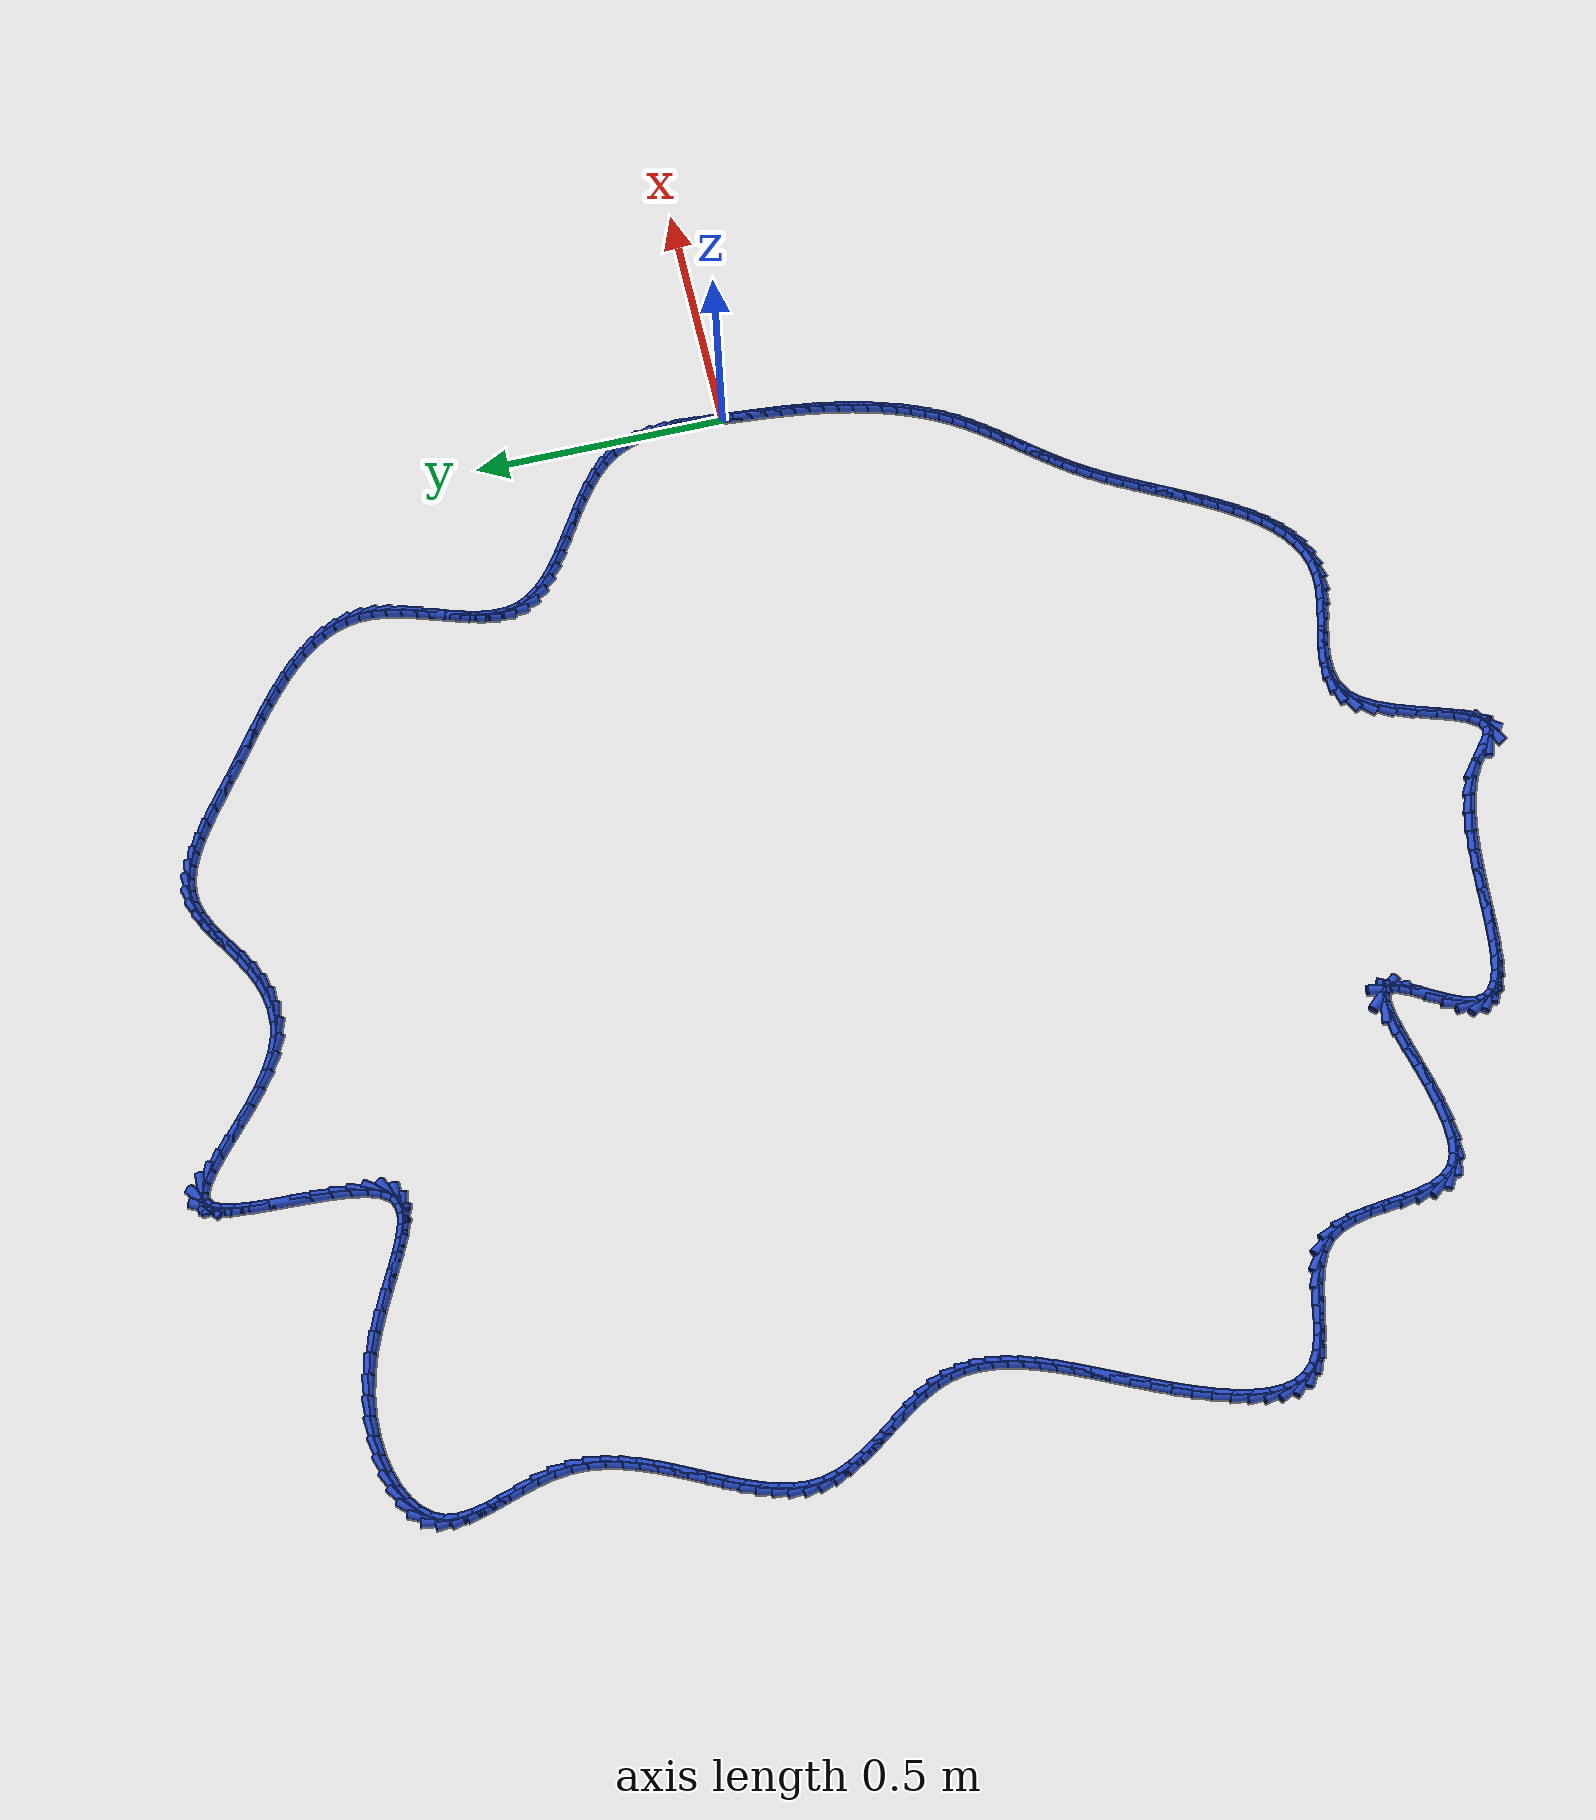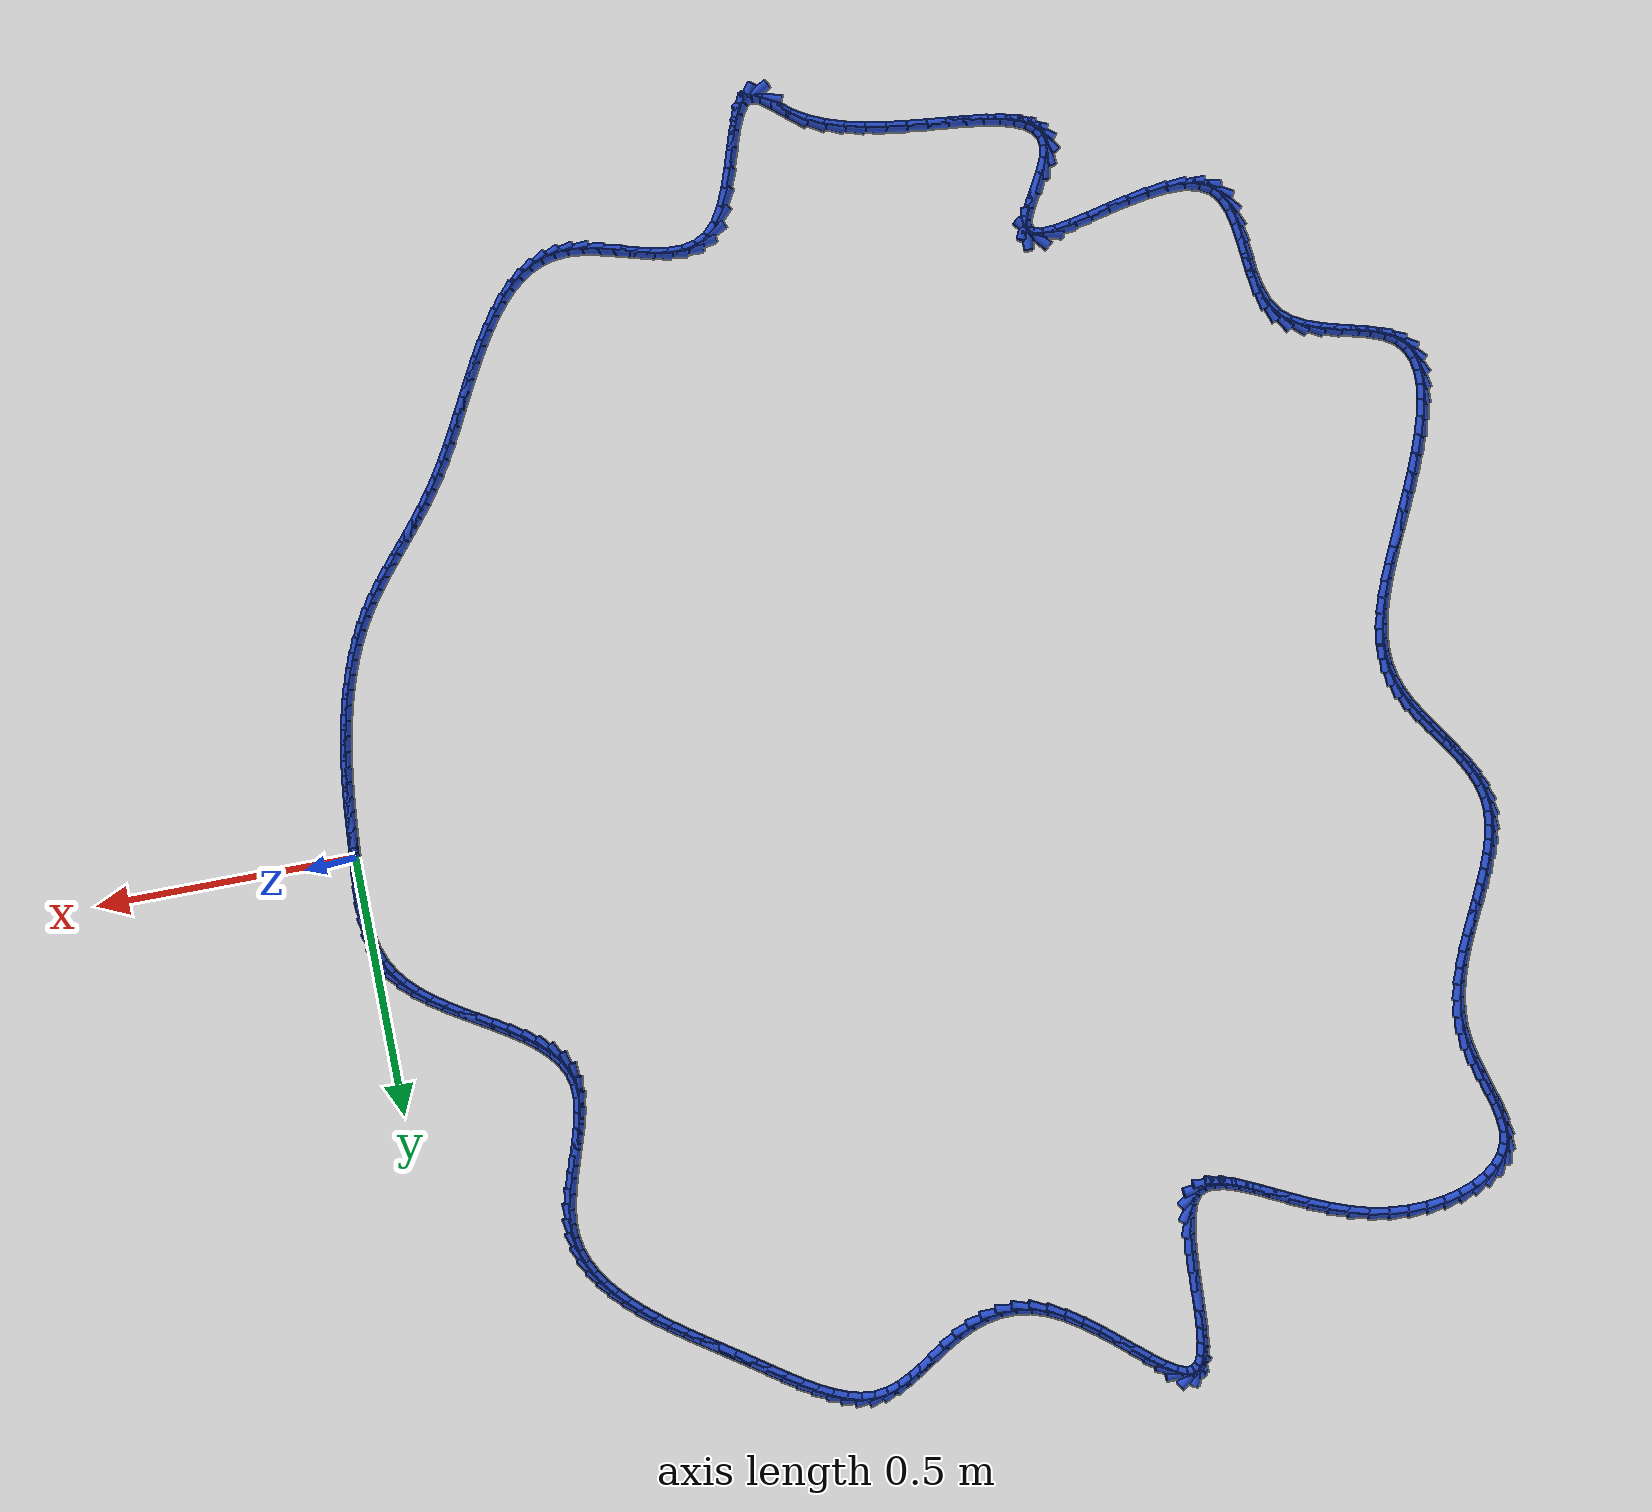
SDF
<sdf version="1.6">
 <world name="default">
  <light name="sun" type="directional">
   <pose>0 0 10 0 -0 0</pose>
   <diffuse>0.8 0.8 0.8 1</diffuse>
   <specular>0.2 0.2 0.2 1</specular>
   <attenuation>
    <range>1000</range>
    <constant>0.9</constant>
    <linear>0.01</linear>
    <quadratic>0.001</quadratic>
   </attenuation>
   <direction>-0.5 0.1 -0.9</direction>
  </light>
  <model name="ground_plane">
   <static>1</static>
   <link name="link">
    <collision name="collision">
     <geometry><plane><normal>0 0 1</normal><size>100 100</size></plane></geometry>
     <surface><friction><ode><mu>100</mu><mu2>50</mu2></ode></friction></surface>
    </collision>
    <visual name="visual">
     <cast_shadows>0</cast_shadows>
     <geometry><plane><normal>0 0 1</normal><size>100 100</size></plane></geometry>
     <material>
      <script><uri>file://media/materials/scripts/gazebo.material</uri><name>Gazebo/WhiteGlow</name></script>
     </material>
    </visual>
   </link>
  </model>
  <gravity>0 0 -9.8</gravity>
  <magnetic_field>6e-06 2.3e-05 -4.2e-05</magnetic_field>
  <atmosphere type="adiabatic"/>
  <physics name="default_physics" default="0" type="ode">
   <max_step_size>0.001</max_step_size>
   <real_time_factor>1</real_time_factor>
   <real_time_update_rate>1000</real_time_update_rate>
  </physics>
  <scene><ambient>0.4 0.4 0.4 1</ambient><background>0.7 0.7 0.7 1</background><shadows>1</shadows></scene>
  <spherical_coordinates>
   <surface_model>EARTH_WGS84</surface_model>
   <latitude_deg>0</latitude_deg>
   <longitude_deg>0</longitude_deg>
   <elevation>0</elevation>
   <heading_deg>0</heading_deg>
  </spherical_coordinates>
  <model name="line">
   <link name="link_0">
    <pose>3.469446951953614e-18 5.551115123125783e-17 0.01 0 1.57 1.498330290614627</pose>
    <collision name="collision">
     <geometry><cylinder><radius>0.01</radius><length>0.08</length></cylinder></geometry>
    </collision>
    <visual name="visual">
     <material>
      <script><name>Gazebo/Blue</name><uri>file://media/materials/scripts/gazebo.material</uri></script>
     </material>
     <geometry><cylinder><radius>0.01</radius><length>0.08</length></cylinder></geometry>
    </visual>
   </link>
   <link name="link_1">
    <pose>0.0022079323524022247 0.030415160771085865 0.01 0 1.57 1.5155651712762834</pose>
    <collision name="collision">
     <geometry><cylinder><radius>0.01</radius><length>0.08</length></cylinder></geometry>
    </collision>
    <visual name="visual">
     <material>
      <script><name>Gazebo/Blue</name><uri>file://media/materials/scripts/gazebo.material</uri></script>
     </material>
     <geometry><cylinder><radius>0.01</radius><length>0.08</length></cylinder></geometry>
    </visual>
   </link>
   <link name="link_2">
    <pose>0.0039018380519931055 0.06105335627017318 0.01 0 1.57 1.5514496398924034</pose>
    <collision name="collision">
     <geometry><cylinder><radius>0.01</radius><length>0.08</length></cylinder></geometry>
    </collision>
    <visual name="visual">
     <material>
      <script><name>Gazebo/Blue</name><uri>file://media/materials/scripts/gazebo.material</uri></script>
     </material>
     <geometry><cylinder><radius>0.01</radius><length>0.08</length></cylinder></geometry>
    </visual>
   </link>
   <link name="link_3">
    <pose>0.004492147283200464 0.09156171062314061 0.01 0 1.57 -1.5340823188433497</pose>
    <collision name="collision">
     <geometry><cylinder><radius>0.01</radius><length>0.08</length></cylinder></geometry>
    </collision>
    <visual name="visual">
     <material>
      <script><name>Gazebo/Blue</name><uri>file://media/materials/scripts/gazebo.material</uri></script>
     </material>
     <geometry><cylinder><radius>0.01</radius><length>0.08</length></cylinder></geometry>
    </visual>
   </link>
   <link name="link_4">
    <pose>0.0033892902304521197 0.12158734795586665 0.01 0 1.57 -1.4553277439843841</pose>
    <collision name="collision">
     <geometry><cylinder><radius>0.01</radius><length>0.08</length></cylinder></geometry>
    </collision>
    <visual name="visual">
     <material>
      <script><name>Gazebo/Blue</name><uri>file://media/materials/scripts/gazebo.material</uri></script>
     </material>
     <geometry><cylinder><radius>0.01</radius><length>0.08</length></cylinder></geometry>
    </visual>
   </link>
   <link name="link_5">
    <pose>3.697078175896734e-06 0.15077739239422996 0.01 0 1.57 -1.3509254751311575</pose>
    <collision name="collision">
     <geometry><cylinder><radius>0.01</radius><length>0.08</length></cylinder></geometry>
    </collision>
    <visual name="visual">
     <material>
      <script><name>Gazebo/Blue</name><uri>file://media/materials/scripts/gazebo.material</uri></script>
     </material>
     <geometry><cylinder><radius>0.01</radius><length>0.08</length></cylinder></geometry>
    </visual>
   </link>
   <link name="link_6">
    <pose>-0.006254201989200389 0.17877896806410914 0.01 0 1.57 -1.2187623375297787</pose>
    <collision name="collision">
     <geometry><cylinder><radius>0.01</radius><length>0.08</length></cylinder></geometry>
    </collision>
    <visual name="visual">
     <material>
      <script><name>Gazebo/Blue</name><uri>file://media/materials/scripts/gazebo.material</uri></script>
     </material>
     <geometry><cylinder><radius>0.01</radius><length>0.08</length></cylinder></geometry>
    </visual>
   </link>
   <link name="link_7">
    <pose>-0.015973976787248906 0.2052391990913826 0.01 0 1.57 -1.0601162414800824</pose>
    <collision name="collision">
     <geometry><cylinder><radius>0.01</radius><length>0.08</length></cylinder></geometry>
    </collision>
    <visual name="visual">
     <material>
      <script><name>Gazebo/Blue</name><uri>file://media/materials/scripts/gazebo.material</uri></script>
     </material>
     <geometry><cylinder><radius>0.01</radius><length>0.08</length></cylinder></geometry>
    </visual>
   </link>
   <link name="link_8">
    <pose>-0.02973888764191233 0.22980834411360912 0.01 0 1.57 -0.8993566565316626</pose>
    <collision name="collision">
     <geometry><cylinder><radius>0.01</radius><length>0.08</length></cylinder></geometry>
    </collision>
    <visual name="visual">
     <material>
      <script><name>Gazebo/Blue</name><uri>file://media/materials/scripts/gazebo.material</uri></script>
     </material>
     <geometry><cylinder><radius>0.01</radius><length>0.08</length></cylinder></geometry>
    </visual>
   </link>
   <link name="link_9">
    <pose>-0.04766528565710766 0.25236861910497177 0.01 0 1.57 -0.7711109970541713</pose>
    <collision name="collision">
     <geometry><cylinder><radius>0.01</radius><length>0.08</length></cylinder></geometry>
    </collision>
    <visual name="visual">
     <material>
      <script><name>Gazebo/Blue</name><uri>file://media/materials/scripts/gazebo.material</uri></script>
     </material>
     <geometry><cylinder><radius>0.01</radius><length>0.08</length></cylinder></geometry>
    </visual>
   </link>
   <link name="link_10">
    <pose>-0.06908985146469539 0.27318957504528624 0.01 0 1.57 -0.6757411114535261</pose>
    <collision name="collision">
     <geometry><cylinder><radius>0.01</radius><length>0.08</length></cylinder></geometry>
    </collision>
    <visual name="visual">
     <material>
      <script><name>Gazebo/Blue</name><uri>file://media/materials/scripts/gazebo.material</uri></script>
     </material>
     <geometry><cylinder><radius>0.01</radius><length>0.08</length></cylinder></geometry>
    </visual>
   </link>
   <link name="link_11">
    <pose>-0.0932752014727869 0.29257755751869324 0.01 0 1.57 -0.6085518937526516</pose>
    <collision name="collision">
     <geometry><cylinder><radius>0.01</radius><length>0.08</length></cylinder></geometry>
    </collision>
    <visual name="visual">
     <material>
      <script><name>Gazebo/Blue</name><uri>file://media/materials/scripts/gazebo.material</uri></script>
     </material>
     <geometry><cylinder><radius>0.01</radius><length>0.08</length></cylinder></geometry>
    </visual>
   </link>
   <link name="link_12">
    <pose>-0.11948395208949357 0.31083891210933295 0.01 0 1.57 -0.5652886176346286</pose>
    <collision name="collision">
     <geometry><cylinder><radius>0.01</radius><length>0.08</length></cylinder></geometry>
    </collision>
    <visual name="visual">
     <material>
      <script><name>Gazebo/Blue</name><uri>file://media/materials/scripts/gazebo.material</uri></script>
     </material>
     <geometry><cylinder><radius>0.01</radius><length>0.08</length></cylinder></geometry>
    </visual>
   </link>
   <link name="link_13">
    <pose>-0.1469787197229268 0.32827998440134615 0.01 0 1.57 -0.5430659805599921</pose>
    <collision name="collision">
     <geometry><cylinder><radius>0.01</radius><length>0.08</length></cylinder></geometry>
    </collision>
    <visual name="visual">
     <material>
      <script><name>Gazebo/Blue</name><uri>file://media/materials/scripts/gazebo.material</uri></script>
     </material>
     <geometry><cylinder><radius>0.01</radius><length>0.08</length></cylinder></geometry>
    </visual>
   </link>
   <link name="link_14">
    <pose>-0.17502212078119783 0.345207119978873 0.01 0 1.57 -0.5405977678383085</pose>
    <collision name="collision">
     <geometry><cylinder><radius>0.01</radius><length>0.08</length></cylinder></geometry>
    </collision>
    <visual name="visual">
     <material>
      <script><name>Gazebo/Blue</name><uri>file://media/materials/scripts/gazebo.material</uri></script>
     </material>
     <geometry><cylinder><radius>0.01</radius><length>0.08</length></cylinder></geometry>
    </visual>
   </link>
   <link name="link_15">
    <pose>-0.20287677167241824 0.3619266644260542 0.01 0 1.57 -0.5582781529216244</pose>
    <collision name="collision">
     <geometry><cylinder><radius>0.01</radius><length>0.08</length></cylinder></geometry>
    </collision>
    <visual name="visual">
     <material>
      <script><name>Gazebo/Blue</name><uri>file://media/materials/scripts/gazebo.material</uri></script>
     </material>
     <geometry><cylinder><radius>0.01</radius><length>0.08</length></cylinder></geometry>
    </visual>
   </link>
   <link name="link_16">
    <pose>-0.22980528880469925 0.37874496332703006 0.01 0 1.57 -0.5983449294985728</pose>
    <collision name="collision">
     <geometry><cylinder><radius>0.01</radius><length>0.08</length></cylinder></geometry>
    </collision>
    <visual name="visual">
     <material>
      <script><name>Gazebo/Blue</name><uri>file://media/materials/scripts/gazebo.material</uri></script>
     </material>
     <geometry><cylinder><radius>0.01</radius><length>0.08</length></cylinder></geometry>
    </visual>
   </link>
   <link name="link_17">
    <pose>-0.25507028858615244 0.3959683622659414 0.01 0 1.57 -0.6651627455581808</pose>
    <collision name="collision">
     <geometry><cylinder><radius>0.01</radius><length>0.08</length></cylinder></geometry>
    </collision>
    <visual name="visual">
     <material>
      <script><name>Gazebo/Blue</name><uri>file://media/materials/scripts/gazebo.material</uri></script>
     </material>
     <geometry><cylinder><radius>0.01</radius><length>0.08</length></cylinder></geometry>
    </visual>
   </link>
   <link name="link_18">
    <pose>-0.2779343874248888 0.4139032068269282 0.01 0 1.57 -0.7654109205332545</pose>
    <collision name="collision">
     <geometry><cylinder><radius>0.01</radius><length>0.08</length></cylinder></geometry>
    </collision>
    <visual name="visual">
     <material>
      <script><name>Gazebo/Blue</name><uri>file://media/materials/scripts/gazebo.material</uri></script>
     </material>
     <geometry><cylinder><radius>0.01</radius><length>0.08</length></cylinder></geometry>
    </visual>
   </link>
   <link name="link_19">
    <pose>-0.2976602017290202 0.43285584259413146 0.01 0 1.57 -0.9073202875811928</pose>
    <collision name="collision">
     <geometry><cylinder><radius>0.01</radius><length>0.08</length></cylinder></geometry>
    </collision>
    <visual name="visual">
     <material>
      <script><name>Gazebo/Blue</name><uri>file://media/materials/scripts/gazebo.material</uri></script>
     </material>
     <geometry><cylinder><radius>0.01</radius><length>0.08</length></cylinder></geometry>
    </visual>
   </link>
   <link name="link_20">
    <pose>-0.31351034790665766 0.4531326151516913 0.01 0 1.57 -1.096850853582554</pose>
    <collision name="collision">
     <geometry><cylinder><radius>0.01</radius><length>0.08</length></cylinder></geometry>
    </collision>
    <visual name="visual">
     <material>
      <script><name>Gazebo/Blue</name><uri>file://media/materials/scripts/gazebo.material</uri></script>
     </material>
     <geometry><cylinder><radius>0.01</radius><length>0.08</length></cylinder></geometry>
    </visual>
   </link>
   <link name="link_21">
    <pose>-0.3247474423659125 0.47503987008374815 0.01 0 1.57 -1.327591362405287</pose>
    <collision name="collision">
     <geometry><cylinder><radius>0.01</radius><length>0.08</length></cylinder></geometry>
    </collision>
    <visual name="visual">
     <material>
      <script><name>Gazebo/Blue</name><uri>file://media/materials/scripts/gazebo.material</uri></script>
     </material>
     <geometry><cylinder><radius>0.01</radius><length>0.08</length></cylinder></geometry>
    </visual>
   </link>
   <link name="link_22">
    <pose>-0.33066106477680074 0.49887394678724173 0.01 0 1.57 -1.5443752632145826</pose>
    <collision name="collision">
     <geometry><cylinder><radius>0.01</radius><length>0.08</length></cylinder></geometry>
    </collision>
    <visual name="visual">
     <material>
      <script><name>Gazebo/Blue</name><uri>file://media/materials/scripts/gazebo.material</uri></script>
     </material>
     <geometry><cylinder><radius>0.01</radius><length>0.08</length></cylinder></geometry>
    </visual>
   </link>
   <link name="link_23">
    <pose>-0.33134182901004033 0.524633917281186 0.01 0 1.57 1.4418799400258353</pose>
    <collision name="collision">
     <geometry><cylinder><radius>0.01</radius><length>0.08</length></cylinder></geometry>
    </collision>
    <visual name="visual">
     <material>
      <script><name>Gazebo/Blue</name><uri>file://media/materials/scripts/gazebo.material</uri></script>
     </material>
     <geometry><cylinder><radius>0.01</radius><length>0.08</length></cylinder></geometry>
    </visual>
   </link>
   <link name="link_24">
    <pose>-0.32779698044728367 0.5519786875273395 0.01 0 1.57 1.340014590913003</pose>
    <collision name="collision">
     <geometry><cylinder><radius>0.01</radius><length>0.08</length></cylinder></geometry>
    </collision>
    <visual name="visual">
     <material>
      <script><name>Gazebo/Blue</name><uri>file://media/materials/scripts/gazebo.material</uri></script>
     </material>
     <geometry><cylinder><radius>0.01</radius><length>0.08</length></cylinder></geometry>
    </visual>
   </link>
   <link name="link_25">
    <pose>-0.32108397897142604 0.5805485286612506 0.01 0 1.57 1.2795533711880922</pose>
    <collision name="collision">
     <geometry><cylinder><radius>0.01</radius><length>0.08</length></cylinder></geometry>
    </collision>
    <visual name="visual">
     <material>
      <script><name>Gazebo/Blue</name><uri>file://media/materials/scripts/gazebo.material</uri></script>
     </material>
     <geometry><cylinder><radius>0.01</radius><length>0.08</length></cylinder></geometry>
    </visual>
   </link>
   <link name="link_26">
    <pose>-0.3122602844653627 0.6099837118184683 0.01 0 1.57 1.2521552456360279</pose>
    <collision name="collision">
     <geometry><cylinder><radius>0.01</radius><length>0.08</length></cylinder></geometry>
    </collision>
    <visual name="visual">
     <material>
      <script><name>Gazebo/Blue</name><uri>file://media/materials/scripts/gazebo.material</uri></script>
     </material>
     <geometry><cylinder><radius>0.01</radius><length>0.08</length></cylinder></geometry>
    </visual>
   </link>
   <link name="link_27">
    <pose>-0.3023833568119891 0.6399245081345416 0.01 0 1.57 1.2537253050259503</pose>
    <collision name="collision">
     <geometry><cylinder><radius>0.01</radius><length>0.08</length></cylinder></geometry>
    </collision>
    <visual name="visual">
     <material>
      <script><name>Gazebo/Blue</name><uri>file://media/materials/scripts/gazebo.material</uri></script>
     </material>
     <geometry><cylinder><radius>0.01</radius><length>0.08</length></cylinder></geometry>
    </visual>
   </link>
   <link name="link_28">
    <pose>-0.29251065589420017 0.670011188745019 0.01 0 1.57 1.2839783187587765</pose>
    <collision name="collision">
     <geometry><cylinder><radius>0.01</radius><length>0.08</length></cylinder></geometry>
    </collision>
    <visual name="visual">
     <material>
      <script><name>Gazebo/Blue</name><uri>file://media/materials/scripts/gazebo.material</uri></script>
     </material>
     <geometry><cylinder><radius>0.01</radius><length>0.08</length></cylinder></geometry>
    </visual>
   </link>
   <link name="link_29">
    <pose>-0.28369964159489147 0.6998840247854494 0.01 0 1.57 1.3462507991636254</pose>
    <collision name="collision">
     <geometry><cylinder><radius>0.01</radius><length>0.08</length></cylinder></geometry>
    </collision>
    <visual name="visual">
     <material>
      <script><name>Gazebo/Blue</name><uri>file://media/materials/scripts/gazebo.material</uri></script>
     </material>
     <geometry><cylinder><radius>0.01</radius><length>0.08</length></cylinder></geometry>
    </visual>
   </link>
   <link name="link_30">
    <pose>-0.2770077737969581 0.7291832873913813 0.01 0 1.57 1.4474995937967319</pose>
    <collision name="collision">
     <geometry><cylinder><radius>0.01</radius><length>0.08</length></cylinder></geometry>
    </collision>
    <visual name="visual">
     <material>
      <script><name>Gazebo/Blue</name><uri>file://media/materials/scripts/gazebo.material</uri></script>
     </material>
     <geometry><cylinder><radius>0.01</radius><length>0.08</length></cylinder></geometry>
    </visual>
   </link>
   <link name="link_31">
    <pose>-0.27349251238329536 0.7575492476983636 0.01 0 1.57 -1.549735292296543</pose>
    <collision name="collision">
     <geometry><cylinder><radius>0.01</radius><length>0.08</length></cylinder></geometry>
    </collision>
    <visual name="visual">
     <material>
      <script><name>Gazebo/Blue</name><uri>file://media/materials/scripts/gazebo.material</uri></script>
     </material>
     <geometry><cylinder><radius>0.01</radius><length>0.08</length></cylinder></geometry>
    </visual>
   </link>
   <link name="link_32">
    <pose>-0.27406382932211953 0.7846719640060903 0.01 0 1.57 -1.3922014786764056</pose>
    <collision name="collision">
     <geometry><cylinder><radius>0.01</radius><length>0.08</length></cylinder></geometry>
    </collision>
    <visual name="visual">
     <material>
      <script><name>Gazebo/Blue</name><uri>file://media/materials/scripts/gazebo.material</uri></script>
     </material>
     <geometry><cylinder><radius>0.01</radius><length>0.08</length></cylinder></geometry>
    </visual>
   </link>
   <link name="link_33">
    <pose>-0.2787342813471977 0.8105444330596276 0.01 0 1.57 -1.2417288068916015</pose>
    <collision name="collision">
     <geometry><cylinder><radius>0.01</radius><length>0.08</length></cylinder></geometry>
    </collision>
    <visual name="visual">
     <material>
      <script><name>Gazebo/Blue</name><uri>file://media/materials/scripts/gazebo.material</uri></script>
     </material>
     <geometry><cylinder><radius>0.01</radius><length>0.08</length></cylinder></geometry>
    </visual>
   </link>
   <link name="link_34">
    <pose>-0.2871788781669887 0.8352735965953476 0.01 0 1.57 -1.1055751893098997</pose>
    <collision name="collision">
     <geometry><cylinder><radius>0.01</radius><length>0.08</length></cylinder></geometry>
    </collision>
    <visual name="visual">
     <material>
      <script><name>Gazebo/Blue</name><uri>file://media/materials/scripts/gazebo.material</uri></script>
     </material>
     <geometry><cylinder><radius>0.01</radius><length>0.08</length></cylinder></geometry>
    </visual>
   </link>
   <link name="link_35">
    <pose>-0.29907201971968467 0.8589666021884015 0.01 0 1.57 -0.9876727680534427</pose>
    <collision name="collision">
     <geometry><cylinder><radius>0.01</radius><length>0.08</length></cylinder></geometry>
    </collision>
    <visual name="visual">
     <material>
      <script><name>Gazebo/Blue</name><uri>file://media/materials/scripts/gazebo.material</uri></script>
     </material>
     <geometry><cylinder><radius>0.01</radius><length>0.08</length></cylinder></geometry>
    </visual>
   </link>
   <link name="link_36">
    <pose>-0.31408810594347736 0.8817305974139413 0.01 0 1.57 -0.8888793751144966</pose>
    <collision name="collision">
     <geometry><cylinder><radius>0.01</radius><length>0.08</length></cylinder></geometry>
    </collision>
    <visual name="visual">
     <material>
      <script><name>Gazebo/Blue</name><uri>file://media/materials/scripts/gazebo.material</uri></script>
     </material>
     <geometry><cylinder><radius>0.01</radius><length>0.08</length></cylinder></geometry>
    </visual>
   </link>
   <link name="link_37">
    <pose>-0.331901536776559 0.9036727298471181 0.01 0 1.57 -0.8080920019695839</pose>
    <collision name="collision">
     <geometry><cylinder><radius>0.01</radius><length>0.08</length></cylinder></geometry>
    </collision>
    <visual name="visual">
     <material>
      <script><name>Gazebo/Blue</name><uri>file://media/materials/scripts/gazebo.material</uri></script>
     </material>
     <geometry><cylinder><radius>0.01</radius><length>0.08</length></cylinder></geometry>
    </visual>
   </link>
   <link name="link_38">
    <pose>-0.35218671215712105 0.9249001470630835 0.01 0 1.57 -0.7433458245390401</pose>
    <collision name="collision">
     <geometry><cylinder><radius>0.01</radius><length>0.08</length></cylinder></geometry>
    </collision>
    <visual name="visual">
     <material>
      <script><name>Gazebo/Blue</name><uri>file://media/materials/scripts/gazebo.material</uri></script>
     </material>
     <geometry><cylinder><radius>0.01</radius><length>0.08</length></cylinder></geometry>
    </visual>
   </link>
   <link name="link_39">
    <pose>-0.374618032023356 0.9455199966369892 0.01 0 1.57 -0.6925329728596181</pose>
    <collision name="collision">
     <geometry><cylinder><radius>0.01</radius><length>0.08</length></cylinder></geometry>
    </collision>
    <visual name="visual">
     <material>
      <script><name>Gazebo/Blue</name><uri>file://media/materials/scripts/gazebo.material</uri></script>
     </material>
     <geometry><cylinder><radius>0.01</radius><length>0.08</length></cylinder></geometry>
    </visual>
   </link>
   <link name="link_40">
    <pose>-0.3988698963134552 0.9656394261439866 0.01 0 1.57 -0.6537631039490145</pose>
    <collision name="collision">
     <geometry><cylinder><radius>0.01</radius><length>0.08</length></cylinder></geometry>
    </collision>
    <visual name="visual">
     <material>
      <script><name>Gazebo/Blue</name><uri>file://media/materials/scripts/gazebo.material</uri></script>
     </material>
     <geometry><cylinder><radius>0.01</radius><length>0.08</length></cylinder></geometry>
    </visual>
   </link>
   <link name="link_41">
    <pose>-0.4246167049656112 0.9853655831592272 0.01 0 1.57 -0.6254994043652939</pose>
    <collision name="collision">
     <geometry><cylinder><radius>0.01</radius><length>0.08</length></cylinder></geometry>
    </collision>
    <visual name="visual">
     <material>
      <script><name>Gazebo/Blue</name><uri>file://media/materials/scripts/gazebo.material</uri></script>
     </material>
     <geometry><cylinder><radius>0.01</radius><length>0.08</length></cylinder></geometry>
    </visual>
   </link>
   <link name="link_42">
    <pose>-0.45153285791801556 1.004805615257863 0.01 0 1.57 -0.6065828659534458</pose>
    <collision name="collision">
     <geometry><cylinder><radius>0.01</radius><length>0.08</length></cylinder></geometry>
    </collision>
    <visual name="visual">
     <material>
      <script><name>Gazebo/Blue</name><uri>file://media/materials/scripts/gazebo.material</uri></script>
     </material>
     <geometry><cylinder><radius>0.01</radius><length>0.08</length></cylinder></geometry>
    </visual>
   </link>
   <link name="link_43">
    <pose>-0.4792927551088602 1.024066670015045 0.01 0 1.57 -0.5962125570922455</pose>
    <collision name="collision">
     <geometry><cylinder><radius>0.01</radius><length>0.08</length></cylinder></geometry>
    </collision>
    <visual name="visual">
     <material>
      <script><name>Gazebo/Blue</name><uri>file://media/materials/scripts/gazebo.material</uri></script>
     </material>
     <geometry><cylinder><radius>0.01</radius><length>0.08</length></cylinder></geometry>
    </visual>
   </link>
   <link name="link_44">
    <pose>-0.5075707964763374 1.0432558950059245 0.01 0 1.57 -0.593916085844543</pose>
    <collision name="collision">
     <geometry><cylinder><radius>0.01</radius><length>0.08</length></cylinder></geometry>
    </collision>
    <visual name="visual">
     <material>
      <script><name>Gazebo/Blue</name><uri>file://media/materials/scripts/gazebo.material</uri></script>
     </material>
     <geometry><cylinder><radius>0.01</radius><length>0.08</length></cylinder></geometry>
    </visual>
   </link>
   <link name="link_45">
    <pose>-0.5360413819586386 1.0624804378056534 0.01 0 1.57 -0.5995219418135074</pose>
    <collision name="collision">
     <geometry><cylinder><radius>0.01</radius><length>0.08</length></cylinder></geometry>
    </collision>
    <visual name="visual">
     <material>
      <script><name>Gazebo/Blue</name><uri>file://media/materials/scripts/gazebo.material</uri></script>
     </material>
     <geometry><cylinder><radius>0.01</radius><length>0.08</length></cylinder></geometry>
    </visual>
   </link>
   <link name="link_46">
    <pose>-0.5643789610953457 1.0818473376550897 0.01 0 1.57 -0.6078675938707381</pose>
    <collision name="collision">
     <geometry><cylinder><radius>0.01</radius><length>0.08</length></cylinder></geometry>
    </collision>
    <visual name="visual">
     <material>
      <script><name>Gazebo/Blue</name><uri>file://media/materials/scripts/gazebo.material</uri></script>
     </material>
     <geometry><cylinder><radius>0.01</radius><length>0.08</length></cylinder></geometry>
    </visual>
   </link>
   <link name="link_47">
    <pose>-0.5923341956937188 1.1012971787352988 0.01 0 1.57 -0.6029806124443239</pose>
    <collision name="collision">
     <geometry><cylinder><radius>0.01</radius><length>0.08</length></cylinder></geometry>
    </collision>
    <visual name="visual">
     <material>
      <script><name>Gazebo/Blue</name><uri>file://media/materials/scripts/gazebo.material</uri></script>
     </material>
     <geometry><cylinder><radius>0.01</radius><length>0.08</length></cylinder></geometry>
    </visual>
   </link>
   <link name="link_48">
    <pose>-0.6198876824722556 1.1202683448524844 0.01 0 1.57 -0.5808232307339538</pose>
    <collision name="collision">
     <geometry><cylinder><radius>0.01</radius><length>0.08</length></cylinder></geometry>
    </collision>
    <visual name="visual">
     <material>
      <script><name>Gazebo/Blue</name><uri>file://media/materials/scripts/gazebo.material</uri></script>
     </material>
     <geometry><cylinder><radius>0.01</radius><length>0.08</length></cylinder></geometry>
    </visual>
   </link>
   <link name="link_49">
    <pose>-0.6470632098422603 1.138104884923891 0.01 0 1.57 -0.5391341168677953</pose>
    <collision name="collision">
     <geometry><cylinder><radius>0.01</radius><length>0.08</length></cylinder></geometry>
    </collision>
    <visual name="visual">
     <material>
      <script><name>Gazebo/Blue</name><uri>file://media/materials/scripts/gazebo.material</uri></script>
     </material>
     <geometry><cylinder><radius>0.01</radius><length>0.08</length></cylinder></geometry>
    </visual>
   </link>
   <link name="link_50">
    <pose>-0.6738845662150379 1.1541508478667641 0.01 0 1.57 -0.47427924475330885</pose>
    <collision name="collision">
     <geometry><cylinder><radius>0.01</radius><length>0.08</length></cylinder></geometry>
    </collision>
    <visual name="visual">
     <material>
      <script><name>Gazebo/Blue</name><uri>file://media/materials/scripts/gazebo.material</uri></script>
     </material>
     <geometry><cylinder><radius>0.01</radius><length>0.08</length></cylinder></geometry>
    </visual>
   </link>
   <link name="link_51">
    <pose>-0.7003755400018931 1.167750282598349 0.01 0 1.57 -0.38127007604198465</pose>
    <collision name="collision">
     <geometry><cylinder><radius>0.01</radius><length>0.08</length></cylinder></geometry>
    </collision>
    <visual name="visual">
     <material>
      <script><name>Gazebo/Blue</name><uri>file://media/materials/scripts/gazebo.material</uri></script>
     </material>
     <geometry><cylinder><radius>0.01</radius><length>0.08</length></cylinder></geometry>
    </visual>
   </link>
   <link name="link_52">
    <pose>-0.7265599196141309 1.1782472380358906 0.01 0 1.57 -0.2545168949227195</pose>
    <collision name="collision">
     <geometry><cylinder><radius>0.01</radius><length>0.08</length></cylinder></geometry>
    </collision>
    <visual name="visual">
     <material>
      <script><name>Gazebo/Blue</name><uri>file://media/materials/scripts/gazebo.material</uri></script>
     </material>
     <geometry><cylinder><radius>0.01</radius><length>0.08</length></cylinder></geometry>
    </visual>
   </link>
   <link name="link_53">
    <pose>-0.7524614934630555 1.1849857630966336 0.01 0 1.57 -0.09038921569735227</pose>
    <collision name="collision">
     <geometry><cylinder><radius>0.01</radius><length>0.08</length></cylinder></geometry>
    </collision>
    <visual name="visual">
     <material>
      <script><name>Gazebo/Blue</name><uri>file://media/materials/scripts/gazebo.material</uri></script>
     </material>
     <geometry><cylinder><radius>0.01</radius><length>0.08</length></cylinder></geometry>
    </visual>
   </link>
   <link name="link_54">
    <pose>-0.7781040499599722 1.1873099066978243 0.01 0 1.57 0.10761917203161885</pose>
    <collision name="collision">
     <geometry><cylinder><radius>0.01</radius><length>0.08</length></cylinder></geometry>
    </collision>
    <visual name="visual">
     <material>
      <script><name>Gazebo/Blue</name><uri>file://media/materials/scripts/gazebo.material</uri></script>
     </material>
     <geometry><cylinder><radius>0.01</radius><length>0.08</length></cylinder></geometry>
    </visual>
   </link>
   <link name="link_55">
    <pose>-0.8035114600831365 1.184564976910733 0.01 0 1.57 0.30572611753320583</pose>
    <collision name="collision">
     <geometry><cylinder><radius>0.01</radius><length>0.08</length></cylinder></geometry>
    </collision>
    <visual name="visual">
     <material>
      <script><name>Gazebo/Blue</name><uri>file://media/materials/scripts/gazebo.material</uri></script>
     </material>
     <geometry><cylinder><radius>0.01</radius><length>0.08</length></cylinder></geometry>
    </visual>
   </link>
   <link name="link_56">
    <pose>-0.8287407608603821 1.1766020672856214 0.01 0 1.57 0.4462342181812535</pose>
    <collision name="collision">
     <geometry><cylinder><radius>0.01</radius><length>0.08</length></cylinder></geometry>
    </collision>
    <visual name="visual">
     <material>
      <script><name>Gazebo/Blue</name><uri>file://media/materials/scripts/gazebo.material</uri></script>
     </material>
     <geometry><cylinder><radius>0.01</radius><length>0.08</length></cylinder></geometry>
    </visual>
   </link>
   <link name="link_57">
    <pose>-0.8539327570992618 1.1645497381536123 0.01 0 1.57 0.5295856027865574</pose>
    <collision name="collision">
     <geometry><cylinder><radius>0.01</radius><length>0.08</length></cylinder></geometry>
    </collision>
    <visual name="visual">
     <material>
      <script><name>Gazebo/Blue</name><uri>file://media/materials/scripts/gazebo.material</uri></script>
     </material>
     <geometry><cylinder><radius>0.01</radius><length>0.08</length></cylinder></geometry>
    </visual>
   </link>
   <link name="link_58">
    <pose>-0.8792412752781241 1.1497351315908677 0.01 0 1.57 0.5659575321430156</pose>
    <collision name="collision">
     <geometry><cylinder><radius>0.01</radius><length>0.08</length></cylinder></geometry>
    </collision>
    <visual name="visual">
     <material>
      <script><name>Gazebo/Blue</name><uri>file://media/materials/scripts/gazebo.material</uri></script>
     </material>
     <geometry><cylinder><radius>0.01</radius><length>0.08</length></cylinder></geometry>
    </visual>
   </link>
   <link name="link_59">
    <pose>-0.9048201418753185 1.1334853896735506 0.01 0 1.57 0.5615207566334015</pose>
    <collision name="collision">
     <geometry><cylinder><radius>0.01</radius><length>0.08</length></cylinder></geometry>
    </collision>
    <visual name="visual">
     <material>
      <script><name>Gazebo/Blue</name><uri>file://media/materials/scripts/gazebo.material</uri></script>
     </material>
     <geometry><cylinder><radius>0.01</radius><length>0.08</length></cylinder></geometry>
    </visual>
   </link>
   <link name="link_60">
    <pose>-0.9308231833691936 1.1171276544778241 0.01 0 1.57 0.5177104476991635</pose>
    <collision name="collision">
     <geometry><cylinder><radius>0.01</radius><length>0.08</length></cylinder></geometry>
    </collision>
    <visual name="visual">
     <material>
      <script><name>Gazebo/Blue</name><uri>file://media/materials/scripts/gazebo.material</uri></script>
     </material>
     <geometry><cylinder><radius>0.01</radius><length>0.08</length></cylinder></geometry>
    </visual>
   </link>
   <link name="link_61">
    <pose>-0.957404226238099 1.101989068079851 0.01 0 1.57 0.4323057126807264</pose>
    <collision name="collision">
     <geometry><cylinder><radius>0.01</radius><length>0.08</length></cylinder></geometry>
    </collision>
    <visual name="visual">
     <material>
      <script><name>Gazebo/Blue</name><uri>file://media/materials/scripts/gazebo.material</uri></script>
     </material>
     <geometry><cylinder><radius>0.01</radius><length>0.08</length></cylinder></geometry>
    </visual>
   </link>
   <link name="link_62">
    <pose>-0.9847143466415075 1.0893877780699792 0.01 0 1.57 0.31312571724454863</pose>
    <collision name="collision">
     <geometry><cylinder><radius>0.01</radius><length>0.08</length></cylinder></geometry>
    </collision>
    <visual name="visual">
     <material>
      <script><name>Gazebo/Blue</name><uri>file://media/materials/scripts/gazebo.material</uri></script>
     </material>
     <geometry><cylinder><radius>0.01</radius><length>0.08</length></cylinder></geometry>
    </visual>
   </link>
   <link name="link_63">
    <pose>-1.012798467338605 1.0802947740194124 0.01 0 1.57 0.17423308863286674</pose>
    <collision name="collision">
     <geometry><cylinder><radius>0.01</radius><length>0.08</length></cylinder></geometry>
    </collision>
    <visual name="visual">
     <material>
      <script><name>Gazebo/Blue</name><uri>file://media/materials/scripts/gazebo.material</uri></script>
     </material>
     <geometry><cylinder><radius>0.01</radius><length>0.08</length></cylinder></geometry>
    </visual>
   </link>
   <link name="link_64">
    <pose>-1.0415640551477052 1.075231517438792 0.01 0 1.57 0.01846573675931245</pose>
    <collision name="collision">
     <geometry><cylinder><radius>0.01</radius><length>0.08</length></cylinder></geometry>
    </collision>
    <visual name="visual">
     <material>
      <script><name>Gazebo/Blue</name><uri>file://media/materials/scripts/gazebo.material</uri></script>
     </material>
     <geometry><cylinder><radius>0.01</radius><length>0.08</length></cylinder></geometry>
    </visual>
   </link>
   <link name="link_65">
    <pose>-1.0709094347101296 1.0746895717851266 0.01 0 1.57 -0.14880482752871935</pose>
    <collision name="collision">
     <geometry><cylinder><radius>0.01</radius><length>0.08</length></cylinder></geometry>
    </collision>
    <visual name="visual">
     <material>
      <script><name>Gazebo/Blue</name><uri>file://media/materials/scripts/gazebo.material</uri></script>
     </material>
     <geometry><cylinder><radius>0.01</radius><length>0.08</length></cylinder></geometry>
    </visual>
   </link>
   <link name="link_66">
    <pose>-1.1007329306671996 1.0791605005154237 0.01 0 1.57 -0.3189151159483015</pose>
    <collision name="collision">
     <geometry><cylinder><radius>0.01</radius><length>0.08</length></cylinder></geometry>
    </collision>
    <visual name="visual">
     <material>
      <script><name>Gazebo/Blue</name><uri>file://media/materials/scripts/gazebo.material</uri></script>
     </material>
     <geometry><cylinder><radius>0.01</radius><length>0.08</length></cylinder></geometry>
    </visual>
   </link>
   <link name="link_67">
    <pose>-1.1309323005242296 1.0891319039916918 0.01 0 1.57 -0.4682939210323814</pose>
    <collision name="collision">
     <geometry><cylinder><radius>0.01</radius><length>0.08</length></cylinder></geometry>
    </collision>
    <visual name="visual">
     <material>
      <script><name>Gazebo/Blue</name><uri>file://media/materials/scripts/gazebo.material</uri></script>
     </material>
     <geometry><cylinder><radius>0.01</radius><length>0.08</length></cylinder></geometry>
    </visual>
   </link>
   <link name="link_68">
    <pose>-1.1613211343509775 1.1045032281665672 0.01 0 1.57 -0.5722279336925387</pose>
    <collision name="collision">
     <geometry><cylinder><radius>0.01</radius><length>0.08</length></cylinder></geometry>
    </collision>
    <visual name="visual">
     <material>
      <script><name>Gazebo/Blue</name><uri>file://media/materials/scripts/gazebo.material</uri></script>
     </material>
     <geometry><cylinder><radius>0.01</radius><length>0.08</length></cylinder></geometry>
    </visual>
   </link>
   <link name="link_69">
    <pose>-1.191540447212336 1.1239679805037117 0.01 0 1.57 -0.6402918925971709</pose>
    <collision name="collision">
     <geometry><cylinder><radius>0.01</radius><length>0.08</length></cylinder></geometry>
    </collision>
    <visual name="visual">
     <material>
      <script><name>Gazebo/Blue</name><uri>file://media/materials/scripts/gazebo.material</uri></script>
     </material>
     <geometry><cylinder><radius>0.01</radius><length>0.08</length></cylinder></geometry>
    </visual>
   </link>
   <link name="link_70">
    <pose>-1.221210092996484 1.1460717960823008 0.01 0 1.57 -0.6810031316759714</pose>
    <collision name="collision">
     <geometry><cylinder><radius>0.01</radius><length>0.08</length></cylinder></geometry>
    </collision>
    <visual name="visual">
     <material>
      <script><name>Gazebo/Blue</name><uri>file://media/materials/scripts/gazebo.material</uri></script>
     </material>
     <geometry><cylinder><radius>0.01</radius><length>0.08</length></cylinder></geometry>
    </visual>
   </link>
   <link name="link_71">
    <pose>-1.2499499255916002 1.1693603099815102 0.01 0 1.57 -0.6981841285572328</pose>
    <collision name="collision">
     <geometry><cylinder><radius>0.01</radius><length>0.08</length></cylinder></geometry>
    </collision>
    <visual name="visual">
     <material>
      <script><name>Gazebo/Blue</name><uri>file://media/materials/scripts/gazebo.material</uri></script>
     </material>
     <geometry><cylinder><radius>0.01</radius><length>0.08</length></cylinder></geometry>
    </visual>
   </link>
   <link name="link_72">
    <pose>-1.277379798885864 1.1923791572805156 0.01 0 1.57 -0.6911740922703492</pose>
    <collision name="collision">
     <geometry><cylinder><radius>0.01</radius><length>0.08</length></cylinder></geometry>
    </collision>
    <visual name="visual">
     <material>
      <script><name>Gazebo/Blue</name><uri>file://media/materials/scripts/gazebo.material</uri></script>
     </material>
     <geometry><cylinder><radius>0.01</radius><length>0.08</length></cylinder></geometry>
    </visual>
   </link>
   <link name="link_73">
    <pose>-1.3031195667674549 1.2136739730584933 0.01 0 1.57 -0.653278388608991</pose>
    <collision name="collision">
     <geometry><cylinder><radius>0.01</radius><length>0.08</length></cylinder></geometry>
    </collision>
    <visual name="visual">
     <material>
      <script><name>Gazebo/Blue</name><uri>file://media/materials/scripts/gazebo.material</uri></script>
     </material>
     <geometry><cylinder><radius>0.01</radius><length>0.08</length></cylinder></geometry>
    </visual>
   </link>
   <link name="link_74">
    <pose>-1.3267890831245506 1.2317903923946183 0.01 0 1.57 -0.5660776129743206</pose>
    <collision name="collision">
     <geometry><cylinder><radius>0.01</radius><length>0.08</length></cylinder></geometry>
    </collision>
    <visual name="visual">
     <material>
      <script><name>Gazebo/Blue</name><uri>file://media/materials/scripts/gazebo.material</uri></script>
     </material>
     <geometry><cylinder><radius>0.01</radius><length>0.08</length></cylinder></geometry>
    </visual>
   </link>
   <link name="link_75">
    <pose>-1.3480082018453312 1.2452740503680673 0.01 0 1.57 -0.3824317665724326</pose>
    <collision name="collision">
     <geometry><cylinder><radius>0.01</radius><length>0.08</length></cylinder></geometry>
    </collision>
    <visual name="visual">
     <material>
      <script><name>Gazebo/Blue</name><uri>file://media/materials/scripts/gazebo.material</uri></script>
     </material>
     <geometry><cylinder><radius>0.01</radius><length>0.08</length></cylinder></geometry>
    </visual>
   </link>
   <link name="link_76">
    <pose>-1.3663967768179746 1.252670582058015 0.01 0 1.57 0.009550415357632583</pose>
    <collision name="collision">
     <geometry><cylinder><radius>0.01</radius><length>0.08</length></cylinder></geometry>
    </collision>
    <visual name="visual">
     <material>
      <script><name>Gazebo/Blue</name><uri>file://media/materials/scripts/gazebo.material</uri></script>
     </material>
     <geometry><cylinder><radius>0.01</radius><length>0.08</length></cylinder></geometry>
    </visual>
   </link>
   <link name="link_77">
    <pose>-1.3815746619306608 1.2525256225436383 0.01 0 1.57 0.6607619640350573</pose>
    <collision name="collision">
     <geometry><cylinder><radius>0.01</radius><length>0.08</length></cylinder></geometry>
    </collision>
    <visual name="visual">
     <material>
      <script><name>Gazebo/Blue</name><uri>file://media/materials/scripts/gazebo.material</uri></script>
     </material>
     <geometry><cylinder><radius>0.01</radius><length>0.08</length></cylinder></geometry>
    </visual>
   </link>
   <link name="link_78">
    <pose>-1.393198279149301 1.2434902761553497 0.01 0 1.57 1.1317001936058362</pose>
    <collision name="collision">
     <geometry><cylinder><radius>0.01</radius><length>0.08</length></cylinder></geometry>
    </collision>
    <visual name="visual">
     <material>
      <script><name>Gazebo/Blue</name><uri>file://media/materials/scripts/gazebo.material</uri></script>
     </material>
     <geometry><cylinder><radius>0.01</radius><length>0.08</length></cylinder></geometry>
    </visual>
   </link>
   <link name="link_79">
    <pose>-1.4014876510909278 1.2258411780787781 0.01 0 1.57 1.347257348268384</pose>
    <collision name="collision">
     <geometry><cylinder><radius>0.01</radius><length>0.08</length></cylinder></geometry>
    </collision>
    <visual name="visual">
     <material>
      <script><name>Gazebo/Blue</name><uri>file://media/materials/scripts/gazebo.material</uri></script>
     </material>
     <geometry><cylinder><radius>0.01</radius><length>0.08</length></cylinder></geometry>
    </visual>
   </link>
   <link name="link_80">
    <pose>-1.4071052230052408 1.2011309940346764 0.01 0 1.57 1.4514332131560044</pose>
    <collision name="collision">
     <geometry><cylinder><radius>0.01</radius><length>0.08</length></cylinder></geometry>
    </collision>
    <visual name="visual">
     <material>
      <script><name>Gazebo/Blue</name><uri>file://media/materials/scripts/gazebo.material</uri></script>
     </material>
     <geometry><cylinder><radius>0.01</radius><length>0.08</length></cylinder></geometry>
    </visual>
   </link>
   <link name="link_81">
    <pose>-1.4107253265207036 1.170946672307879 0.01 0 1.57 1.5034821313970972</pose>
    <collision name="collision">
     <geometry><cylinder><radius>0.01</radius><length>0.08</length></cylinder></geometry>
    </collision>
    <visual name="visual">
     <material>
      <script><name>Gazebo/Blue</name><uri>file://media/materials/scripts/gazebo.material</uri></script>
     </material>
     <geometry><cylinder><radius>0.01</radius><length>0.08</length></cylinder></geometry>
    </visual>
   </link>
   <link name="link_82">
    <pose>-1.4130222932657803 1.1368751611832195 0.01 0 1.57 1.5255129740757205</pose>
    <collision name="collision">
     <geometry><cylinder><radius>0.01</radius><length>0.08</length></cylinder></geometry>
    </collision>
    <visual name="visual">
     <material>
      <script><name>Gazebo/Blue</name><uri>file://media/materials/scripts/gazebo.material</uri></script>
     </material>
     <geometry><cylinder><radius>0.01</radius><length>0.08</length></cylinder></geometry>
    </visual>
   </link>
   <link name="link_83">
    <pose>-1.4146704548689353 1.1005034089455346 0.01 0 1.57 1.5256958518511423</pose>
    <collision name="collision">
     <geometry><cylinder><radius>0.01</radius><length>0.08</length></cylinder></geometry>
    </collision>
    <visual name="visual">
     <material>
      <script><name>Gazebo/Blue</name><uri>file://media/materials/scripts/gazebo.material</uri></script>
     </material>
     <geometry><cylinder><radius>0.01</radius><length>0.08</length></cylinder></geometry>
    </visual>
   </link>
   <link name="link_84">
    <pose>-1.4163441429586323 1.063418363879658 0.01 0 1.57 1.5053430059126676</pose>
    <collision name="collision">
     <geometry><cylinder><radius>0.01</radius><length>0.08</length></cylinder></geometry>
    </collision>
    <visual name="visual">
     <material>
      <script><name>Gazebo/Blue</name><uri>file://media/materials/scripts/gazebo.material</uri></script>
     </material>
     <geometry><cylinder><radius>0.01</radius><length>0.08</length></cylinder></geometry>
    </visual>
   </link>
   <link name="link_85">
    <pose>-1.4187176891633355 1.0272069742704246 0.01 0 1.57 1.4602079251436888</pose>
    <collision name="collision">
     <geometry><cylinder><radius>0.01</radius><length>0.08</length></cylinder></geometry>
    </collision>
    <visual name="visual">
     <material>
      <script><name>Gazebo/Blue</name><uri>file://media/materials/scripts/gazebo.material</uri></script>
     </material>
     <geometry><cylinder><radius>0.01</radius><length>0.08</length></cylinder></geometry>
    </visual>
   </link>
   <link name="link_86">
    <pose>-1.4224654251115088 0.9934561884026691 0.01 0 1.57 1.3780792104758186</pose>
    <collision name="collision">
     <geometry><cylinder><radius>0.01</radius><length>0.08</length></cylinder></geometry>
    </collision>
    <visual name="visual">
     <material>
      <script><name>Gazebo/Blue</name><uri>file://media/materials/scripts/gazebo.material</uri></script>
     </material>
     <geometry><cylinder><radius>0.01</radius><length>0.08</length></cylinder></geometry>
    </visual>
   </link>
   <link name="link_87">
    <pose>-1.4282616824316166 0.9637529545612261 0.01 0 1.57 1.2306075809647454</pose>
    <collision name="collision">
     <geometry><cylinder><radius>0.01</radius><length>0.08</length></cylinder></geometry>
    </collision>
    <visual name="visual">
     <material>
      <script><name>Gazebo/Blue</name><uri>file://media/materials/scripts/gazebo.material</uri></script>
     </material>
     <geometry><cylinder><radius>0.01</radius><length>0.08</length></cylinder></geometry>
    </visual>
   </link>
   <link name="link_88">
    <pose>-1.4367807927521228 0.939684221030931 0.01 0 1.57 0.9559648887873313</pose>
    <collision name="collision">
     <geometry><cylinder><radius>0.01</radius><length>0.08</length></cylinder></geometry>
    </collision>
    <visual name="visual">
     <material>
      <script><name>Gazebo/Blue</name><uri>file://media/materials/scripts/gazebo.material</uri></script>
     </material>
     <geometry><cylinder><radius>0.01</radius><length>0.08</length></cylinder></geometry>
    </visual>
   </link>
   <link name="link_89">
    <pose>-1.4486903600210557 0.9228183663506297 0.01 0 1.57 0.5282815217940532</pose>
    <collision name="collision">
     <geometry><cylinder><radius>0.01</radius><length>0.08</length></cylinder></geometry>
    </collision>
    <visual name="visual">
     <material>
      <script><name>Gazebo/Blue</name><uri>file://media/materials/scripts/gazebo.material</uri></script>
     </material>
     <geometry><cylinder><radius>0.01</radius><length>0.08</length></cylinder></geometry>
    </visual>
   </link>
   <link name="link_90">
    <pose>-1.4642918537074452 0.9137131645368668 0.01 0 1.57 0.11997922675049814</pose>
    <collision name="collision">
     <geometry><cylinder><radius>0.01</radius><length>0.08</length></cylinder></geometry>
    </collision>
    <visual name="visual">
     <material>
      <script><name>Gazebo/Blue</name><uri>file://media/materials/scripts/gazebo.material</uri></script>
     </material>
     <geometry><cylinder><radius>0.01</radius><length>0.08</length></cylinder></geometry>
    </visual>
   </link>
   <link name="link_91">
    <pose>-1.4833398210614142 0.9114167746983349 0.01 0 1.57 -0.15357758555110324</pose>
    <collision name="collision">
     <geometry><cylinder><radius>0.01</radius><length>0.08</length></cylinder></geometry>
    </collision>
    <visual name="visual">
     <material>
      <script><name>Gazebo/Blue</name><uri>file://media/materials/scripts/gazebo.material</uri></script>
     </material>
     <geometry><cylinder><radius>0.01</radius><length>0.08</length></cylinder></geometry>
    </visual>
   </link>
   <link name="link_92">
    <pose>-1.5055440886877856 0.9148539180022854 0.01 0 1.57 -0.31233739051770243</pose>
    <collision name="collision">
     <geometry><cylinder><radius>0.01</radius><length>0.08</length></cylinder></geometry>
    </collision>
    <visual name="visual">
     <material>
      <script><name>Gazebo/Blue</name><uri>file://media/materials/scripts/gazebo.material</uri></script>
     </material>
     <geometry><cylinder><radius>0.01</radius><length>0.08</length></cylinder></geometry>
    </visual>
   </link>
   <link name="link_93">
    <pose>-1.5306144831913844 0.9229493156159698 0.01 0 1.57 -0.3996834214147611</pose>
    <collision name="collision">
     <geometry><cylinder><radius>0.01</radius><length>0.08</length></cylinder></geometry>
    </collision>
    <visual name="visual">
     <material>
      <script><name>Gazebo/Blue</name><uri>file://media/materials/scripts/gazebo.material</uri></script>
     </material>
     <geometry><cylinder><radius>0.01</radius><length>0.08</length></cylinder></geometry>
    </visual>
   </link>
   <link name="link_94">
    <pose>-1.558260831177034 0.9346276887066393 0.01 0 1.57 -0.4425841245334084</pose>
    <collision name="collision">
     <geometry><cylinder><radius>0.01</radius><length>0.08</length></cylinder></geometry>
    </collision>
    <visual name="visual">
     <material>
      <script><name>Gazebo/Blue</name><uri>file://media/materials/scripts/gazebo.material</uri></script>
     </material>
     <geometry><cylinder><radius>0.01</radius><length>0.08</length></cylinder></geometry>
    </visual>
   </link>
   <link name="link_95">
    <pose>-1.5881929592495598 0.9488137584415455 0.01 0 1.57 -0.45495617971721114</pose>
    <collision name="collision">
     <geometry><cylinder><radius>0.01</radius><length>0.08</length></cylinder></geometry>
    </collision>
    <visual name="visual">
     <material>
      <script><name>Gazebo/Blue</name><uri>file://media/materials/scripts/gazebo.material</uri></script>
     </material>
     <geometry><cylinder><radius>0.01</radius><length>0.08</length></cylinder></geometry>
    </visual>
   </link>
   <link name="link_96">
    <pose>-1.620120694013785 0.9644322459879396 0.01 0 1.57 -0.44344522388283564</pose>
    <collision name="collision">
     <geometry><cylinder><radius>0.01</radius><length>0.08</length></cylinder></geometry>
    </collision>
    <visual name="visual">
     <material>
      <script><name>Gazebo/Blue</name><uri>file://media/materials/scripts/gazebo.material</uri></script>
     </material>
     <geometry><cylinder><radius>0.01</radius><length>0.08</length></cylinder></geometry>
    </visual>
   </link>
   <link name="link_97">
    <pose>-1.6537538620745333 0.980407872513073 0.01 0 1.57 -0.41058412466750055</pose>
    <collision name="collision">
     <geometry><cylinder><radius>0.01</radius><length>0.08</length></cylinder></geometry>
    </collision>
    <visual name="visual">
     <material>
      <script><name>Gazebo/Blue</name><uri>file://media/materials/scripts/gazebo.material</uri></script>
     </material>
     <geometry><cylinder><radius>0.01</radius><length>0.08</length></cylinder></geometry>
    </visual>
   </link>
   <link name="link_98">
    <pose>-1.6888022900366297 0.9956653591841974 0.01 0 1.57 -0.3563205607134158</pose>
    <collision name="collision">
     <geometry><cylinder><radius>0.01</radius><length>0.08</length></cylinder></geometry>
    </collision>
    <visual name="visual">
     <material>
      <script><name>Gazebo/Blue</name><uri>file://media/materials/scripts/gazebo.material</uri></script>
     </material>
     <geometry><cylinder><radius>0.01</radius><length>0.08</length></cylinder></geometry>
    </visual>
   </link>
   <link name="link_99">
    <pose>-1.7249758045048984 1.0091294271685638 0.01 0 1.57 -0.27883949510979833</pose>
    <collision name="collision">
     <geometry><cylinder><radius>0.01</radius><length>0.08</length></cylinder></geometry>
    </collision>
    <visual name="visual">
     <material>
      <script><name>Gazebo/Blue</name><uri>file://media/materials/scripts/gazebo.material</uri></script>
     </material>
     <geometry><cylinder><radius>0.01</radius><length>0.08</length></cylinder></geometry>
    </visual>
   </link>
   <link name="link_100">
    <pose>-1.7619842069642184 1.0197248691457574 0.01 0 1.57 -0.18211839078773046</pose>
    <collision name="collision">
     <geometry><cylinder><radius>0.01</radius><length>0.08</length></cylinder></geometry>
    </collision>
    <visual name="visual">
     <material>
      <script><name>Gazebo/Blue</name><uri>file://media/materials/scripts/gazebo.material</uri></script>
     </material>
     <geometry><cylinder><radius>0.01</radius><length>0.08</length></cylinder></geometry>
    </visual>
   </link>
   <link name="link_101">
    <pose>-1.7994501565377172 1.0266245576995257 0.01 0 1.57 -0.08513958704428101</pose>
    <collision name="collision">
     <geometry><cylinder><radius>0.01</radius><length>0.08</length></cylinder></geometry>
    </collision>
    <visual name="visual">
     <material>
      <script><name>Gazebo/Blue</name><uri>file://media/materials/scripts/gazebo.material</uri></script>
     </material>
     <geometry><cylinder><radius>0.01</radius><length>0.08</length></cylinder></geometry>
    </visual>
   </link>
   <link name="link_102">
    <pose>-1.8367140640891886 1.0298048795681447 0.01 0 1.57 0.01101258214515627</pose>
    <collision name="collision">
     <geometry><cylinder><radius>0.01</radius><length>0.08</length></cylinder></geometry>
    </collision>
    <visual name="visual">
     <material>
      <script><name>Gazebo/Blue</name><uri>file://media/materials/scripts/gazebo.material</uri></script>
     </material>
     <geometry><cylinder><radius>0.01</radius><length>0.08</length></cylinder></geometry>
    </visual>
   </link>
   <link name="link_103">
    <pose>-1.873059299233742 1.0294046084991793 0.01 0 1.57 0.11024258815331767</pose>
    <collision name="collision">
     <geometry><cylinder><radius>0.01</radius><length>0.08</length></cylinder></geometry>
    </collision>
    <visual name="visual">
     <material>
      <script><name>Gazebo/Blue</name><uri>file://media/materials/scripts/gazebo.material</uri></script>
     </material>
     <geometry><cylinder><radius>0.01</radius><length>0.08</length></cylinder></geometry>
    </visual>
   </link>
   <link name="link_104">
    <pose>-1.9077692315864865 1.0255625182401924 0.01 0 1.57 0.21732766815232155</pose>
    <collision name="collision">
     <geometry><cylinder><radius>0.01</radius><length>0.08</length></cylinder></geometry>
    </collision>
    <visual name="visual">
     <material>
      <script><name>Gazebo/Blue</name><uri>file://media/materials/scripts/gazebo.material</uri></script>
     </material>
     <geometry><cylinder><radius>0.01</radius><length>0.08</length></cylinder></geometry>
    </visual>
   </link>
   <link name="link_105">
    <pose>-1.9401272307625312 1.0184173825387492 0.01 0 1.57 0.33844104684467274</pose>
    <collision name="collision">
     <geometry><cylinder><radius>0.01</radius><length>0.08</length></cylinder></geometry>
    </collision>
    <visual name="visual">
     <material>
      <script><name>Gazebo/Blue</name><uri>file://media/materials/scripts/gazebo.material</uri></script>
     </material>
     <geometry><cylinder><radius>0.01</radius><length>0.08</length></cylinder></geometry>
    </visual>
   </link>
   <link name="link_106">
    <pose>-1.9694166663769856 1.0081079751424131 0.01 0 1.57 0.481760449741731</pose>
    <collision name="collision">
     <geometry><cylinder><radius>0.01</radius><length>0.08</length></cylinder></geometry>
    </collision>
    <visual name="visual">
     <material>
      <script><name>Gazebo/Blue</name><uri>file://media/materials/scripts/gazebo.material</uri></script>
     </material>
     <geometry><cylinder><radius>0.01</radius><length>0.08</length></cylinder></geometry>
    </visual>
   </link>
   <link name="link_107">
    <pose>-1.994920908044958 0.9947730697987478 0.01 0 1.57 0.6576646419309105</pose>
    <collision name="collision">
     <geometry><cylinder><radius>0.01</radius><length>0.08</length></cylinder></geometry>
    </collision>
    <visual name="visual">
     <material>
      <script><name>Gazebo/Blue</name><uri>file://media/materials/scripts/gazebo.material</uri></script>
     </material>
     <geometry><cylinder><radius>0.01</radius><length>0.08</length></cylinder></geometry>
    </visual>
   </link>
   <link name="link_108">
    <pose>-2.0159233253815585 0.9785514402553174 0.01 0 1.57 0.8768058261167104</pose>
    <collision name="collision">
     <geometry><cylinder><radius>0.01</radius><length>0.08</length></cylinder></geometry>
    </collision>
    <visual name="visual">
     <material>
      <script><name>Gazebo/Blue</name><uri>file://media/materials/scripts/gazebo.material</uri></script>
     </material>
     <geometry><cylinder><radius>0.01</radius><length>0.08</length></cylinder></geometry>
    </visual>
   </link>
   <link name="link_109">
    <pose>-2.0317072880018965 0.9595818602596857 0.01 0 1.57 1.142620151649802</pose>
    <collision name="collision">
     <geometry><cylinder><radius>0.01</radius><length>0.08</length></cylinder></geometry>
    </collision>
    <visual name="visual">
     <material>
      <script><name>Gazebo/Blue</name><uri>file://media/materials/scripts/gazebo.material</uri></script>
     </material>
     <geometry><cylinder><radius>0.01</radius><length>0.08</length></cylinder></geometry>
    </visual>
   </link>
   <link name="link_110">
    <pose>-2.0415561655210803 0.938003103559417 0.01 0 1.57 1.4251434250210107</pose>
    <collision name="collision">
     <geometry><cylinder><radius>0.01</radius><length>0.08</length></cylinder></geometry>
    </collision>
    <visual name="visual">
     <material>
      <script><name>Gazebo/Blue</name><uri>file://media/materials/scripts/gazebo.material</uri></script>
     </material>
     <geometry><cylinder><radius>0.01</radius><length>0.08</length></cylinder></geometry>
    </visual>
   </link>
   <link name="link_111">
    <pose>-2.0450787075971104 0.9139898723724422 0.01 0 1.57 -1.5035816060234533</pose>
    <collision name="collision">
     <geometry><cylinder><radius>0.01</radius><length>0.08</length></cylinder></geometry>
    </collision>
    <visual name="visual">
     <material>
      <script><name>Gazebo/Blue</name><uri>file://media/materials/scripts/gazebo.material</uri></script>
     </material>
     <geometry><cylinder><radius>0.01</radius><length>0.08</length></cylinder></geometry>
    </visual>
   </link>
   <link name="link_112">
    <pose>-2.043320793053385 0.8878755567457736 0.01 0 1.57 -1.3724267211832306</pose>
    <collision name="collision">
     <geometry><cylinder><radius>0.01</radius><length>0.08</length></cylinder></geometry>
    </collision>
    <visual name="visual">
     <material>
      <script><name>Gazebo/Blue</name><uri>file://media/materials/scripts/gazebo.material</uri></script>
     </material>
     <geometry><cylinder><radius>0.01</radius><length>0.08</length></cylinder></geometry>
    </visual>
   </link>
   <link name="link_113">
    <pose>-2.037724944712695 0.8600373441641876 0.01 0 1.57 -1.3035328572244878</pose>
    <collision name="collision">
     <geometry><cylinder><radius>0.01</radius><length>0.08</length></cylinder></geometry>
    </collision>
    <visual name="visual">
     <material>
      <script><name>Gazebo/Blue</name><uri>file://media/materials/scripts/gazebo.material</uri></script>
     </material>
     <geometry><cylinder><radius>0.01</radius><length>0.08</length></cylinder></geometry>
    </visual>
   </link>
   <link name="link_114">
    <pose>-2.0297336983505194 0.8308524235426986 0.01 0 1.57 -1.2824525113524032</pose>
    <collision name="collision">
     <geometry><cylinder><radius>0.01</radius><length>0.08</length></cylinder></geometry>
    </collision>
    <visual name="visual">
     <material>
      <script><name>Gazebo/Blue</name><uri>file://media/materials/scripts/gazebo.material</uri></script>
     </material>
     <geometry><cylinder><radius>0.01</radius><length>0.08</length></cylinder></geometry>
    </visual>
   </link>
   <link name="link_115">
    <pose>-2.020789589742339 0.8006979837963196 0.01 0 1.57 -1.3024581355600389</pose>
    <collision name="collision">
     <geometry><cylinder><radius>0.01</radius><length>0.08</length></cylinder></geometry>
    </collision>
    <visual name="visual">
     <material>
      <script><name>Gazebo/Blue</name><uri>file://media/materials/scripts/gazebo.material</uri></script>
     </material>
     <geometry><cylinder><radius>0.01</radius><length>0.08</length></cylinder></geometry>
    </visual>
   </link>
   <link name="link_116">
    <pose>-2.0123351546636337 0.7699512138400636 0.01 0 1.57 -1.363178601462297</pose>
    <collision name="collision">
     <geometry><cylinder><radius>0.01</radius><length>0.08</length></cylinder></geometry>
    </collision>
    <visual name="visual">
     <material>
      <script><name>Gazebo/Blue</name><uri>file://media/materials/scripts/gazebo.material</uri></script>
     </material>
     <geometry><cylinder><radius>0.01</radius><length>0.08</length></cylinder></geometry>
    </visual>
   </link>
   <link name="link_117">
    <pose>-2.005812928889881 0.7389893025889431 0.01 0 1.57 -1.468480324550072</pose>
    <collision name="collision">
     <geometry><cylinder><radius>0.01</radius><length>0.08</length></cylinder></geometry>
    </collision>
    <visual name="visual">
     <material>
      <script><name>Gazebo/Blue</name><uri>file://media/materials/scripts/gazebo.material</uri></script>
     </material>
     <geometry><cylinder><radius>0.01</radius><length>0.08</length></cylinder></geometry>
    </visual>
   </link>
   <link name="link_118">
    <pose>-2.0026502649711344 0.7081864960272543 0.01 0 1.57 1.542910128136743</pose>
    <collision name="collision">
     <geometry><cylinder><radius>0.01</radius><length>0.08</length></cylinder></geometry>
    </collision>
    <visual name="visual">
     <material>
      <script><name>Gazebo/Blue</name><uri>file://media/materials/scripts/gazebo.material</uri></script>
     </material>
     <geometry><cylinder><radius>0.01</radius><length>0.08</length></cylinder></geometry>
    </visual>
   </link>
   <link name="link_119">
    <pose>-2.0034987779427125 0.6777666806671037 0.01 0 1.57 1.4259459317180836</pose>
    <collision name="collision">
     <geometry><cylinder><radius>0.01</radius><length>0.08</length></cylinder></geometry>
    </collision>
    <visual name="visual">
     <material>
      <script><name>Gazebo/Blue</name><uri>file://media/materials/scripts/gazebo.material</uri></script>
     </material>
     <geometry><cylinder><radius>0.01</radius><length>0.08</length></cylinder></geometry>
    </visual>
   </link>
   <link name="link_120">
    <pose>-2.007879614778914 0.647734626917854 0.01 0 1.57 1.3280149104617016</pose>
    <collision name="collision">
     <geometry><cylinder><radius>0.01</radius><length>0.08</length></cylinder></geometry>
    </collision>
    <visual name="visual">
     <material>
      <script><name>Gazebo/Blue</name><uri>file://media/materials/scripts/gazebo.material</uri></script>
     </material>
     <geometry><cylinder><radius>0.01</radius><length>0.08</length></cylinder></geometry>
    </visual>
   </link>
   <link name="link_121">
    <pose>-2.0152246241479865 0.6180777966973867 0.01 0 1.57 1.2497735999832393</pose>
    <collision name="collision">
     <geometry><cylinder><radius>0.01</radius><length>0.08</length></cylinder></geometry>
    </collision>
    <visual name="visual">
     <material>
      <script><name>Gazebo/Blue</name><uri>file://media/materials/scripts/gazebo.material</uri></script>
     </material>
     <geometry><cylinder><radius>0.01</radius><length>0.08</length></cylinder></geometry>
    </visual>
   </link>
   <link name="link_122">
    <pose>-2.0249656547181756 0.5887836519235833 0.01 0 1.57 1.1905490536556496</pose>
    <collision name="collision">
     <geometry><cylinder><radius>0.01</radius><length>0.08</length></cylinder></geometry>
    </collision>
    <visual name="visual">
     <material>
      <script><name>Gazebo/Blue</name><uri>file://media/materials/scripts/gazebo.material</uri></script>
     </material>
     <geometry><cylinder><radius>0.01</radius><length>0.08</length></cylinder></geometry>
    </visual>
   </link>
   <link name="link_123">
    <pose>-2.0365345551577296 0.5598396545143264 0.01 0 1.57 1.149229678133355</pose>
    <collision name="collision">
     <geometry><cylinder><radius>0.01</radius><length>0.08</length></cylinder></geometry>
    </collision>
    <visual name="visual">
     <material>
      <script><name>Gazebo/Blue</name><uri>file://media/materials/scripts/gazebo.material</uri></script>
     </material>
     <geometry><cylinder><radius>0.01</radius><length>0.08</length></cylinder></geometry>
    </visual>
   </link>
   <link name="link_124">
    <pose>-2.0493631741348945 0.5312332663874972 0.01 0 1.57 1.1248536973077818</pose>
    <collision name="collision">
     <geometry><cylinder><radius>0.01</radius><length>0.08</length></cylinder></geometry>
    </collision>
    <visual name="visual">
     <material>
      <script><name>Gazebo/Blue</name><uri>file://media/materials/scripts/gazebo.material</uri></script>
     </material>
     <geometry><cylinder><radius>0.01</radius><length>0.08</length></cylinder></geometry>
    </visual>
   </link>
   <link name="link_125">
    <pose>-2.062883360317916 0.5029519494609775 0.01 0 1.57 1.1169438663822806</pose>
    <collision name="collision">
     <geometry><cylinder><radius>0.01</radius><length>0.08</length></cylinder></geometry>
    </collision>
    <visual name="visual">
     <material>
      <script><name>Gazebo/Blue</name><uri>file://media/materials/scripts/gazebo.material</uri></script>
     </material>
     <geometry><cylinder><radius>0.01</radius><length>0.08</length></cylinder></geometry>
    </visual>
   </link>
   <link name="link_126">
    <pose>-2.0765269623750435 0.47498316565264864 0.01 0 1.57 1.125692280943015</pose>
    <collision name="collision">
     <geometry><cylinder><radius>0.01</radius><length>0.08</length></cylinder></geometry>
    </collision>
    <visual name="visual">
     <material>
      <script><name>Gazebo/Blue</name><uri>file://media/materials/scripts/gazebo.material</uri></script>
     </material>
     <geometry><cylinder><radius>0.01</radius><length>0.08</length></cylinder></geometry>
    </visual>
   </link>
   <link name="link_127">
    <pose>-2.089725828974522 0.44731437688039305 0.01 0 1.57 1.152068937846194</pose>
    <collision name="collision">
     <geometry><cylinder><radius>0.01</radius><length>0.08</length></cylinder></geometry>
    </collision>
    <visual name="visual">
     <material>
      <script><name>Gazebo/Blue</name><uri>file://media/materials/scripts/gazebo.material</uri></script>
     </material>
     <geometry><cylinder><radius>0.01</radius><length>0.08</length></cylinder></geometry>
    </visual>
   </link>
   <link name="link_128">
    <pose>-2.1019118087845983 0.4199330450620923 0.01 0 1.57 1.1978698905211755</pose>
    <collision name="collision">
     <geometry><cylinder><radius>0.01</radius><length>0.08</length></cylinder></geometry>
    </collision>
    <visual name="visual">
     <material>
      <script><name>Gazebo/Blue</name><uri>file://media/materials/scripts/gazebo.material</uri></script>
     </material>
     <geometry><cylinder><radius>0.01</radius><length>0.08</length></cylinder></geometry>
    </visual>
   </link>
   <link name="link_129">
    <pose>-2.112516750473519 0.39282663211562774 0.01 0 1.57 1.2656394975356575</pose>
    <collision name="collision">
     <geometry><cylinder><radius>0.01</radius><length>0.08</length></cylinder></geometry>
    </collision>
    <visual name="visual">
     <material>
      <script><name>Gazebo/Blue</name><uri>file://media/materials/scripts/gazebo.material</uri></script>
     </material>
     <geometry><cylinder><radius>0.01</radius><length>0.08</length></cylinder></geometry>
    </visual>
   </link>
   <link name="link_130">
    <pose>-2.1209725027095327 0.36598259995888144 0.01 0 1.57 1.3582777219472795</pose>
    <collision name="collision">
     <geometry><cylinder><radius>0.01</radius><length>0.08</length></cylinder></geometry>
    </collision>
    <visual name="visual">
     <material>
      <script><name>Gazebo/Blue</name><uri>file://media/materials/scripts/gazebo.material</uri></script>
     </material>
     <geometry><cylinder><radius>0.01</radius><length>0.08</length></cylinder></geometry>
    </visual>
   </link>
   <link name="link_131">
    <pose>-2.1267109141608853 0.3393884105097346 0.01 0 1.57 1.477998024554266</pose>
    <collision name="collision">
     <geometry><cylinder><radius>0.01</radius><length>0.08</length></cylinder></geometry>
    </collision>
    <visual name="visual">
     <material>
      <script><name>Gazebo/Blue</name><uri>file://media/materials/scripts/gazebo.material</uri></script>
     </material>
     <geometry><cylinder><radius>0.01</radius><length>0.08</length></cylinder></geometry>
    </visual>
   </link>
   <link name="link_132">
    <pose>-2.1291638334958223 0.3130315256860697 0.01 0 1.57 -1.5172459442200044</pose>
    <collision name="collision">
     <geometry><cylinder><radius>0.01</radius><length>0.08</length></cylinder></geometry>
    </collision>
    <visual name="visual">
     <material>
      <script><name>Gazebo/Blue</name><uri>file://media/materials/scripts/gazebo.material</uri></script>
     </material>
     <geometry><cylinder><radius>0.01</radius><length>0.08</length></cylinder></geometry>
    </visual>
   </link>
   <link name="link_133">
    <pose>-2.1277631093825917 0.2868994074057681 0.01 0 1.57 -1.3507930163217925</pose>
    <collision name="collision">
     <geometry><cylinder><radius>0.01</radius><length>0.08</length></cylinder></geometry>
    </collision>
    <visual name="visual">
     <material>
      <script><name>Gazebo/Blue</name><uri>file://media/materials/scripts/gazebo.material</uri></script>
     </material>
     <geometry><cylinder><radius>0.01</radius><length>0.08</length></cylinder></geometry>
    </visual>
   </link>
   <link name="link_134">
    <pose>-2.1219667308932157 0.26097908102942047 0.01 0 1.57 -1.1993577352950455</pose>
    <collision name="collision">
     <geometry><cylinder><radius>0.01</radius><length>0.08</length></cylinder></geometry>
    </collision>
    <visual name="visual">
     <material>
      <script><name>Gazebo/Blue</name><uri>file://media/materials/scripts/gazebo.material</uri></script>
     </material>
     <geometry><cylinder><radius>0.01</radius><length>0.08</length></cylinder></geometry>
    </visual>
   </link>
   <link name="link_135">
    <pose>-2.11194309060859 0.23524570783800514 0.01 0 1.57 -1.0912224670594124</pose>
    <collision name="collision">
     <geometry><cylinder><radius>0.01</radius><length>0.08</length></cylinder></geometry>
    </collision>
    <visual name="visual">
     <material>
      <script><name>Gazebo/Blue</name><uri>file://media/materials/scripts/gazebo.material</uri></script>
     </material>
     <geometry><cylinder><radius>0.01</radius><length>0.08</length></cylinder></geometry>
    </visual>
   </link>
   <link name="link_136">
    <pose>-2.098637515357775 0.20966147393760737 0.01 0 1.57 -1.0212322283032311</pose>
    <collision name="collision">
     <geometry><cylinder><radius>0.01</radius><length>0.08</length></cylinder></geometry>
    </collision>
    <visual name="visual">
     <material>
      <script><name>Gazebo/Blue</name><uri>file://media/materials/scripts/gazebo.material</uri></script>
     </material>
     <geometry><cylinder><radius>0.01</radius><length>0.08</length></cylinder></geometry>
    </visual>
   </link>
   <link name="link_137">
    <pose>-2.0830348119597044 0.18418790609952876 0.01 0 1.57 -0.9833178860788786</pose>
    <collision name="collision">
     <geometry><cylinder><radius>0.01</radius><length>0.08</length></cylinder></geometry>
    </collision>
    <visual name="visual">
     <material>
      <script><name>Gazebo/Blue</name><uri>file://media/materials/scripts/gazebo.material</uri></script>
     </material>
     <geometry><cylinder><radius>0.01</radius><length>0.08</length></cylinder></geometry>
    </visual>
   </link>
   <link name="link_138">
    <pose>-2.066119787233312 0.15878653109507126 0.01 0 1.57 -0.9738209605882284</pose>
    <collision name="collision">
     <geometry><cylinder><radius>0.01</radius><length>0.08</length></cylinder></geometry>
    </collision>
    <visual name="visual">
     <material>
      <script><name>Gazebo/Blue</name><uri>file://media/materials/scripts/gazebo.material</uri></script>
     </material>
     <geometry><cylinder><radius>0.01</radius><length>0.08</length></cylinder></geometry>
    </visual>
   </link>
   <link name="link_139">
    <pose>-2.0488772479975332 0.13341887569553695 0.01 0 1.57 -0.9918436902243039</pose>
    <collision name="collision">
     <geometry><cylinder><radius>0.01</radius><length>0.08</length></cylinder></geometry>
    </collision>
    <visual name="visual">
     <material>
      <script><name>Gazebo/Blue</name><uri>file://media/materials/scripts/gazebo.material</uri></script>
     </material>
     <geometry><cylinder><radius>0.01</radius><length>0.08</length></cylinder></geometry>
    </visual>
   </link>
   <link name="link_140">
    <pose>-2.0322920010713004 0.10804646667222739 0.01 0 1.57 -1.0392835179491355</pose>
    <collision name="collision">
     <geometry><cylinder><radius>0.01</radius><length>0.08</length></cylinder></geometry>
    </collision>
    <visual name="visual">
     <material>
      <script><name>Gazebo/Blue</name><uri>file://media/materials/scripts/gazebo.material</uri></script>
     </material>
     <geometry><cylinder><radius>0.01</radius><length>0.08</length></cylinder></geometry>
    </visual>
   </link>
   <link name="link_141">
    <pose>-2.0173488532735493 0.08263083079644538 0.01 0 1.57 -1.1208082658121743</pose>
    <collision name="collision">
     <geometry><cylinder><radius>0.01</radius><length>0.08</length></cylinder></geometry>
    </collision>
    <visual name="visual">
     <material>
      <script><name>Gazebo/Blue</name><uri>file://media/materials/scripts/gazebo.material</uri></script>
     </material>
     <geometry><cylinder><radius>0.01</radius><length>0.08</length></cylinder></geometry>
    </visual>
   </link>
   <link name="link_142">
    <pose>-2.005032611423214 0.057133494839492545 0.01 0 1.57 -1.2414533679913344</pose>
    <collision name="collision">
     <geometry><cylinder><radius>0.01</radius><length>0.08</length></cylinder></geometry>
    </collision>
    <visual name="visual">
     <material>
      <script><name>Gazebo/Blue</name><uri>file://media/materials/scripts/gazebo.material</uri></script>
     </material>
     <geometry><cylinder><radius>0.01</radius><length>0.08</length></cylinder></geometry>
    </visual>
   </link>
   <link name="link_143">
    <pose>-1.9962763031443065 0.031514591158086844 0.01 0 1.57 -1.3799624518939744</pose>
    <collision name="collision">
     <geometry><cylinder><radius>0.01</radius><length>0.08</length></cylinder></geometry>
    </collision>
    <visual name="visual">
     <material>
      <script><name>Gazebo/Blue</name><uri>file://media/materials/scripts/gazebo.material</uri></script>
     </material>
     <geometry><cylinder><radius>0.01</radius><length>0.08</length></cylinder></geometry>
    </visual>
   </link>
   <link name="link_144">
    <pose>-1.9912921864584656 0.005714841771516518 0.01 0 1.57 -1.5122111269956504</pose>
    <collision name="collision">
     <geometry><cylinder><radius>0.01</radius><length>0.08</length></cylinder></geometry>
    </collision>
    <visual name="visual">
     <material>
      <script><name>Gazebo/Blue</name><uri>file://media/materials/scripts/gazebo.material</uri></script>
     </material>
     <geometry><cylinder><radius>0.01</radius><length>0.08</length></cylinder></geometry>
    </visual>
   </link>
   <link name="link_145">
    <pose>-1.9897640528298925 -0.020339262914148108 0.01 0 1.57 1.5102431524342177</pose>
    <collision name="collision">
     <geometry><cylinder><radius>0.01</radius><length>0.08</length></cylinder></geometry>
    </collision>
    <visual name="visual">
     <material>
      <script><name>Gazebo/Blue</name><uri>file://media/materials/scripts/gazebo.material</uri></script>
     </material>
     <geometry><cylinder><radius>0.01</radius><length>0.08</length></cylinder></geometry>
    </visual>
   </link>
   <link name="link_146">
    <pose>-1.9913635400704 -0.04672155979089934 0.01 0 1.57 1.4080209900042377</pose>
    <collision name="collision">
     <geometry><cylinder><radius>0.01</radius><length>0.08</length></cylinder></geometry>
    </collision>
    <visual name="visual">
     <material>
      <script><name>Gazebo/Blue</name><uri>file://media/materials/scripts/gazebo.material</uri></script>
     </material>
     <geometry><cylinder><radius>0.01</radius><length>0.08</length></cylinder></geometry>
    </visual>
   </link>
   <link name="link_147">
    <pose>-1.9957622859917983 -0.073505885750727 0.01 0 1.57 1.323933644253018</pose>
    <collision name="collision">
     <geometry><cylinder><radius>0.01</radius><length>0.08</length></cylinder></geometry>
    </collision>
    <visual name="visual">
     <material>
      <script><name>Gazebo/Blue</name><uri>file://media/materials/scripts/gazebo.material</uri></script>
     </material>
     <geometry><cylinder><radius>0.01</radius><length>0.08</length></cylinder></geometry>
    </visual>
   </link>
   <link name="link_148">
    <pose>-2.0026319284059 -0.10076607768562347 0.01 0 1.57 1.2574115343491388</pose>
    <collision name="collision">
     <geometry><cylinder><radius>0.01</radius><length>0.08</length></cylinder></geometry>
    </collision>
    <visual name="visual">
     <material>
      <script><name>Gazebo/Blue</name><uri>file://media/materials/scripts/gazebo.material</uri></script>
     </material>
     <geometry><cylinder><radius>0.01</radius><length>0.08</length></cylinder></geometry>
    </visual>
   </link>
   <link name="link_149">
    <pose>-2.0116441051245166 -0.12857597248758018 0.01 0 1.57 1.2069843277178944</pose>
    <collision name="collision">
     <geometry><cylinder><radius>0.01</radius><length>0.08</length></cylinder></geometry>
    </collision>
    <visual name="visual">
     <material>
      <script><name>Gazebo/Blue</name><uri>file://media/materials/scripts/gazebo.material</uri></script>
     </material>
     <geometry><cylinder><radius>0.01</radius><length>0.08</length></cylinder></geometry>
    </visual>
   </link>
   <link name="link_150">
    <pose>-2.02247045395946 -0.15700940704858868 0.01 0 1.57 1.170917209728556</pose>
    <collision name="collision">
     <geometry><cylinder><radius>0.01</radius><length>0.08</length></cylinder></geometry>
    </collision>
    <visual name="visual">
     <material>
      <script><name>Gazebo/Blue</name><uri>file://media/materials/scripts/gazebo.material</uri></script>
     </material>
     <geometry><cylinder><radius>0.01</radius><length>0.08</length></cylinder></geometry>
    </visual>
   </link>
   <link name="link_151">
    <pose>-2.034782612722541 -0.18614021826064045 0.01 0 1.57 1.147561586208824</pose>
    <collision name="collision">
     <geometry><cylinder><radius>0.01</radius><length>0.08</length></cylinder></geometry>
    </collision>
    <visual name="visual">
     <material>
      <script><name>Gazebo/Blue</name><uri>file://media/materials/scripts/gazebo.material</uri></script>
     </material>
     <geometry><cylinder><radius>0.01</radius><length>0.08</length></cylinder></geometry>
    </visual>
   </link>
   <link name="link_152">
    <pose>-2.048252219225572 -0.216042243015727 0.01 0 1.57 1.1355038349042812</pose>
    <collision name="collision">
     <geometry><cylinder><radius>0.01</radius><length>0.08</length></cylinder></geometry>
    </collision>
    <visual name="visual">
     <material>
      <script><name>Gazebo/Blue</name><uri>file://media/materials/scripts/gazebo.material</uri></script>
     </material>
     <geometry><cylinder><radius>0.01</radius><length>0.08</length></cylinder></geometry>
    </visual>
   </link>
   <link name="link_153">
    <pose>-2.0625509112803644 -0.24678931820583977 0.01 0 1.57 1.1335996855342239</pose>
    <collision name="collision">
     <geometry><cylinder><radius>0.01</radius><length>0.08</length></cylinder></geometry>
    </collision>
    <visual name="visual">
     <material>
      <script><name>Gazebo/Blue</name><uri>file://media/materials/scripts/gazebo.material</uri></script>
     </material>
     <geometry><cylinder><radius>0.01</radius><length>0.08</length></cylinder></geometry>
    </visual>
   </link>
   <link name="link_154">
    <pose>-2.07735032669873 -0.2784552807229702 0.01 0 1.57 1.1409576209304424</pose>
    <collision name="collision">
     <geometry><cylinder><radius>0.01</radius><length>0.08</length></cylinder></geometry>
    </collision>
    <visual name="visual">
     <material>
      <script><name>Gazebo/Blue</name><uri>file://media/materials/scripts/gazebo.material</uri></script>
     </material>
     <geometry><cylinder><radius>0.01</radius><length>0.08</length></cylinder></geometry>
    </visual>
   </link>
   <link name="link_155">
    <pose>-2.0923188348650394 -0.31110725530592764 0.01 0 1.57 1.157192149093695</pose>
    <collision name="collision">
     <geometry><cylinder><radius>0.01</radius><length>0.08</length></cylinder></geometry>
    </collision>
    <visual name="visual">
     <material>
      <script><name>Gazebo/Blue</name><uri>file://media/materials/scripts/gazebo.material</uri></script>
     </material>
     <geometry><cylinder><radius>0.01</radius><length>0.08</length></cylinder></geometry>
    </visual>
   </link>
   <link name="link_156">
    <pose>-2.1070028865285737 -0.34456199045925107 0.01 0 1.57 1.1829414277970234</pose>
    <collision name="collision">
     <geometry><cylinder><radius>0.01</radius><length>0.08</length></cylinder></geometry>
    </collision>
    <visual name="visual">
     <material>
      <script><name>Gazebo/Blue</name><uri>file://media/materials/scripts/gazebo.material</uri></script>
     </material>
     <geometry><cylinder><radius>0.01</radius><length>0.08</length></cylinder></geometry>
    </visual>
   </link>
   <link name="link_157">
    <pose>-2.1207934676672737 -0.378316966972747 0.01 0 1.57 1.2197999441622005</pose>
    <collision name="collision">
     <geometry><cylinder><radius>0.01</radius><length>0.08</length></cylinder></geometry>
    </collision>
    <visual name="visual">
     <material>
      <script><name>Gazebo/Blue</name><uri>file://media/materials/scripts/gazebo.material</uri></script>
     </material>
     <geometry><cylinder><radius>0.01</radius><length>0.08</length></cylinder></geometry>
    </visual>
   </link>
   <link name="link_158">
    <pose>-2.133071462101328 -0.4118489195032418 0.01 0 1.57 1.2706711342199997</pose>
    <collision name="collision">
     <geometry><cylinder><radius>0.01</radius><length>0.08</length></cylinder></geometry>
    </collision>
    <visual name="visual">
     <material>
      <script><name>Gazebo/Blue</name><uri>file://media/materials/scripts/gazebo.material</uri></script>
     </material>
     <geometry><cylinder><radius>0.01</radius><length>0.08</length></cylinder></geometry>
    </visual>
   </link>
   <link name="link_159">
    <pose>-2.143217753650927 -0.44463458270756195 0.01 0 1.57 1.340309530448115</pose>
    <collision name="collision">
     <geometry><cylinder><radius>0.01</radius><length>0.08</length></cylinder></geometry>
    </collision>
    <visual name="visual">
     <material>
      <script><name>Gazebo/Blue</name><uri>file://media/materials/scripts/gazebo.material</uri></script>
     </material>
     <geometry><cylinder><radius>0.01</radius><length>0.08</length></cylinder></geometry>
    </visual>
   </link>
   <link name="link_160">
    <pose>-2.1506132261362576 -0.47615069124253406 0.01 0 1.57 1.4361816100632319</pose>
    <collision name="collision">
     <geometry><cylinder><radius>0.01</radius><length>0.08</length></cylinder></geometry>
    </collision>
    <visual name="visual">
     <material>
      <script><name>Gazebo/Blue</name><uri>file://media/materials/scripts/gazebo.material</uri></script>
     </material>
     <geometry><cylinder><radius>0.01</radius><length>0.08</length></cylinder></geometry>
    </visual>
   </link>
   <link name="link_161">
    <pose>-2.15463876337751 -0.5058739797649842 0.01 0 1.57 1.5694650783787067</pose>
    <collision name="collision">
     <geometry><cylinder><radius>0.01</radius><length>0.08</length></cylinder></geometry>
    </collision>
    <visual name="visual">
     <material>
      <script><name>Gazebo/Blue</name><uri>file://media/materials/scripts/gazebo.material</uri></script>
     </material>
     <geometry><cylinder><radius>0.01</radius><length>0.08</length></cylinder></geometry>
    </visual>
   </link>
   <link name="link_162">
    <pose>-2.1546752491948715 -0.5332811829317391 0.01 0 1.57 -1.3868167335781936</pose>
    <collision name="collision">
     <geometry><cylinder><radius>0.01</radius><length>0.08</length></cylinder></geometry>
    </collision>
    <visual name="visual">
     <material>
      <script><name>Gazebo/Blue</name><uri>file://media/materials/scripts/gazebo.material</uri></script>
     </material>
     <geometry><cylinder><radius>0.01</radius><length>0.08</length></cylinder></geometry>
    </visual>
   </link>
   <link name="link_163">
    <pose>-2.1501035674085323 -0.557849035399625 0.01 0 1.57 -1.1379247200459208</pose>
    <collision name="collision">
     <geometry><cylinder><radius>0.01</radius><length>0.08</length></cylinder></geometry>
    </collision>
    <visual name="visual">
     <material>
      <script><name>Gazebo/Blue</name><uri>file://media/materials/scripts/gazebo.material</uri></script>
     </material>
     <geometry><cylinder><radius>0.01</radius><length>0.08</length></cylinder></geometry>
    </visual>
   </link>
   <link name="link_164">
    <pose>-2.1403046018386798 -0.5790542718254692 0.01 0 1.57 -0.8361602571646246</pose>
    <collision name="collision">
     <geometry><cylinder><radius>0.01</radius><length>0.08</length></cylinder></geometry>
    </collision>
    <visual name="visual">
     <material>
      <script><name>Gazebo/Blue</name><uri>file://media/materials/scripts/gazebo.material</uri></script>
     </material>
     <geometry><cylinder><radius>0.01</radius><length>0.08</length></cylinder></geometry>
    </visual>
   </link>
   <link name="link_165">
    <pose>-2.1246596822382173 -0.5963739839282473 0.01 0 1.57 -0.5518134535876208</pose>
    <collision name="collision">
     <geometry><cylinder><radius>0.01</radius><length>0.08</length></cylinder></geometry>
    </collision>
    <visual name="visual">
     <material>
      <script><name>Gazebo/Blue</name><uri>file://media/materials/scripts/gazebo.material</uri></script>
     </material>
     <geometry><cylinder><radius>0.01</radius><length>0.08</length></cylinder></geometry>
    </visual>
   </link>
   <link name="link_166">
    <pose>-2.103043973653063 -0.6096806815842879 0.01 0 1.57 -0.37421000908732027</pose>
    <collision name="collision">
     <geometry><cylinder><radius>0.01</radius><length>0.08</length></cylinder></geometry>
    </collision>
    <visual name="visual">
     <material>
      <script><name>Gazebo/Blue</name><uri>file://media/materials/scripts/gazebo.material</uri></script>
     </material>
     <geometry><cylinder><radius>0.01</radius><length>0.08</length></cylinder></geometry>
    </visual>
   </link>
   <link name="link_167">
    <pose>-2.076770897299272 -0.6199984987288609 0.01 0 1.57 -0.28376980396767204</pose>
    <collision name="collision">
     <geometry><cylinder><radius>0.01</radius><length>0.08</length></cylinder></geometry>
    </collision>
    <visual name="visual">
     <material>
      <script><name>Gazebo/Blue</name><uri>file://media/materials/scripts/gazebo.material</uri></script>
     </material>
     <geometry><cylinder><radius>0.01</radius><length>0.08</length></cylinder></geometry>
    </visual>
   </link>
   <link name="link_168">
    <pose>-2.047414273524552 -0.62856007311677 0.01 0 1.57 -0.2547539694324992</pose>
    <collision name="collision">
     <geometry><cylinder><radius>0.01</radius><length>0.08</length></cylinder></geometry>
    </collision>
    <visual name="visual">
     <material>
      <script><name>Gazebo/Blue</name><uri>file://media/materials/scripts/gazebo.material</uri></script>
     </material>
     <geometry><cylinder><radius>0.01</radius><length>0.08</length></cylinder></geometry>
    </visual>
   </link>
   <link name="link_169">
    <pose>-2.0165479226766103 -0.6365980425028173 0.01 0 1.57 -0.2766888308140119</pose>
    <collision name="collision">
     <geometry><cylinder><radius>0.01</radius><length>0.08</length></cylinder></geometry>
    </collision>
    <visual name="visual">
     <material>
      <script><name>Gazebo/Blue</name><uri>file://media/materials/scripts/gazebo.material</uri></script>
     </material>
     <geometry><cylinder><radius>0.01</radius><length>0.08</length></cylinder></geometry>
    </visual>
   </link>
   <link name="link_170">
    <pose>-1.9857456651031558 -0.6453450446418062 0.01 0 1.57 -0.3512960754035963</pose>
    <collision name="collision">
     <geometry><cylinder><radius>0.01</radius><length>0.08</length></cylinder></geometry>
    </collision>
    <visual name="visual">
     <material>
      <script><name>Gazebo/Blue</name><uri>file://media/materials/scripts/gazebo.material</uri></script>
     </material>
     <geometry><cylinder><radius>0.01</radius><length>0.08</length></cylinder></geometry>
    </visual>
   </link>
   <link name="link_171">
    <pose>-1.9565813211518959 -0.6560337172885393 0.01 0 1.57 -0.4906047438406072</pose>
    <collision name="collision">
     <geometry><cylinder><radius>0.01</radius><length>0.08</length></cylinder></geometry>
    </collision>
    <visual name="visual">
     <material>
      <script><name>Gazebo/Blue</name><uri>file://media/materials/scripts/gazebo.material</uri></script>
     </material>
     <geometry><cylinder><radius>0.01</radius><length>0.08</length></cylinder></geometry>
    </visual>
   </link>
   <link name="link_172">
    <pose>-1.9306287111705374 -0.6698966981978194 0.01 0 1.57 -0.7120676570184888</pose>
    <collision name="collision">
     <geometry><cylinder><radius>0.01</radius><length>0.08</length></cylinder></geometry>
    </collision>
    <visual name="visual">
     <material>
      <script><name>Gazebo/Blue</name><uri>file://media/materials/scripts/gazebo.material</uri></script>
     </material>
     <geometry><cylinder><radius>0.01</radius><length>0.08</length></cylinder></geometry>
    </visual>
   </link>
   <link name="link_173">
    <pose>-1.9094616555067896 -0.6881666251244506 0.01 0 1.57 -0.9996607174795227</pose>
    <collision name="collision">
     <geometry><cylinder><radius>0.01</radius><length>0.08</length></cylinder></geometry>
    </collision>
    <visual name="visual">
     <material>
      <script><name>Gazebo/Blue</name><uri>file://media/materials/scripts/gazebo.material</uri></script>
     </material>
     <geometry><cylinder><radius>0.01</radius><length>0.08</length></cylinder></geometry>
    </visual>
   </link>
   <link name="link_174">
    <pose>-1.8942967705728366 -0.7117669184592839 0.01 0 1.57 -1.2301454766727267</pose>
    <collision name="collision">
     <geometry><cylinder><radius>0.01</radius><length>0.08</length></cylinder></geometry>
    </collision>
    <visual name="visual">
     <material>
      <script><name>Gazebo/Blue</name><uri>file://media/materials/scripts/gazebo.material</uri></script>
     </material>
     <geometry><cylinder><radius>0.01</radius><length>0.08</length></cylinder></geometry>
    </visual>
   </link>
   <link name="link_175">
    <pose>-1.8843334114611496 -0.7398747350007299 0.01 0 1.57 -1.372355714762874</pose>
    <collision name="collision">
     <geometry><cylinder><radius>0.01</radius><length>0.08</length></cylinder></geometry>
    </collision>
    <visual name="visual">
     <material>
      <script><name>Gazebo/Blue</name><uri>file://media/materials/scripts/gazebo.material</uri></script>
     </material>
     <geometry><cylinder><radius>0.01</radius><length>0.08</length></cylinder></geometry>
    </visual>
   </link>
   <link name="link_176">
    <pose>-1.8780634968042595 -0.7710548316950403 0.01 0 1.57 -1.4469437512029955</pose>
    <collision name="collision">
     <geometry><cylinder><radius>0.01</radius><length>0.08</length></cylinder></geometry>
    </collision>
    <visual name="visual">
     <material>
      <script><name>Gazebo/Blue</name><uri>file://media/materials/scripts/gazebo.material</uri></script>
     </material>
     <geometry><cylinder><radius>0.01</radius><length>0.08</length></cylinder></geometry>
    </visual>
   </link>
   <link name="link_177">
    <pose>-1.8739781818689565 -0.8038713046728416 0.01 0 1.57 -1.467894106624035</pose>
    <collision name="collision">
     <geometry><cylinder><radius>0.01</radius><length>0.08</length></cylinder></geometry>
    </collision>
    <visual name="visual">
     <material>
      <script><name>Gazebo/Blue</name><uri>file://media/materials/scripts/gazebo.material</uri></script>
     </material>
     <geometry><cylinder><radius>0.01</radius><length>0.08</length></cylinder></geometry>
    </visual>
   </link>
   <link name="link_178">
    <pose>-1.8705686219220325 -0.8368882500647602 0.01 0 1.57 -1.4380866818928286</pose>
    <collision name="collision">
     <geometry><cylinder><radius>0.01</radius><length>0.08</length></cylinder></geometry>
    </collision>
    <visual name="visual">
     <material>
      <script><name>Gazebo/Blue</name><uri>file://media/materials/scripts/gazebo.material</uri></script>
     </material>
     <geometry><cylinder><radius>0.01</radius><length>0.08</length></cylinder></geometry>
    </visual>
   </link>
   <link name="link_179">
    <pose>-1.866325972230277 -0.8686697640014217 0.01 0 1.57 -1.3483445185715626</pose>
    <collision name="collision">
     <geometry><cylinder><radius>0.01</radius><length>0.08</length></cylinder></geometry>
    </collision>
    <visual name="visual">
     <material>
      <script><name>Gazebo/Blue</name><uri>file://media/materials/scripts/gazebo.material</uri></script>
     </material>
     <geometry><cylinder><radius>0.01</radius><length>0.08</length></cylinder></geometry>
    </visual>
   </link>
   <link name="link_180">
    <pose>-1.8597413880604812 -0.8977799426134527 0.01 0 1.57 -1.1754099309429213</pose>
    <collision name="collision">
     <geometry><cylinder><radius>0.01</radius><length>0.08</length></cylinder></geometry>
    </collision>
    <visual name="visual">
     <material>
      <script><name>Gazebo/Blue</name><uri>file://media/materials/scripts/gazebo.material</uri></script>
     </material>
     <geometry><cylinder><radius>0.01</radius><length>0.08</length></cylinder></geometry>
    </visual>
   </link>
   <link name="link_181">
    <pose>-1.849306024679435 -0.9227828820314801 0.01 0 1.57 -0.8889782421730252</pose>
    <collision name="collision">
     <geometry><cylinder><radius>0.01</radius><length>0.08</length></cylinder></geometry>
    </collision>
    <visual name="visual">
     <material>
      <script><name>Gazebo/Blue</name><uri>file://media/materials/scripts/gazebo.material</uri></script>
     </material>
     <geometry><cylinder><radius>0.01</radius><length>0.08</length></cylinder></geometry>
    </visual>
   </link>
   <link name="link_182">
    <pose>-1.8335110373539292 -0.9422426783861282 0.01 0 1.57 -0.5085805689242043</pose>
    <collision name="collision">
     <geometry><cylinder><radius>0.01</radius><length>0.08</length></cylinder></geometry>
    </collision>
    <visual name="visual">
     <material>
      <script><name>Gazebo/Blue</name><uri>file://media/materials/scripts/gazebo.material</uri></script>
     </material>
     <geometry><cylinder><radius>0.01</radius><length>0.08</length></cylinder></geometry>
    </visual>
   </link>
   <link name="link_183">
    <pose>-1.8109538105990413 -0.9548182566691358 0.01 0 1.57 -0.19739380855250294</pose>
    <collision name="collision">
     <geometry><cylinder><radius>0.01</radius><length>0.08</length></cylinder></geometry>
    </collision>
    <visual name="visual">
     <material>
      <script><name>Gazebo/Blue</name><uri>file://media/materials/scripts/gazebo.material</uri></script>
     </material>
     <geometry><cylinder><radius>0.01</radius><length>0.08</length></cylinder></geometry>
    </visual>
   </link>
   <link name="link_184">
    <pose>-1.7818736333001957 -0.9606342391637637 0.01 0 1.57 -0.00979403591884324</pose>
    <collision name="collision">
     <geometry><cylinder><radius>0.01</radius><length>0.08</length></cylinder></geometry>
    </collision>
    <visual name="visual">
     <material>
      <script><name>Gazebo/Blue</name><uri>file://media/materials/scripts/gazebo.material</uri></script>
     </material>
     <geometry><cylinder><radius>0.01</radius><length>0.08</length></cylinder></geometry>
    </visual>
   </link>
   <link name="link_185">
    <pose>-1.747801083281277 -0.9609679576130042 0.01 0 1.57 0.10204873533520765</pose>
    <collision name="collision">
     <geometry><cylinder><radius>0.01</radius><length>0.08</length></cylinder></geometry>
    </collision>
    <visual name="visual">
     <material>
      <script><name>Gazebo/Blue</name><uri>file://media/materials/scripts/gazebo.material</uri></script>
     </material>
     <geometry><cylinder><radius>0.01</radius><length>0.08</length></cylinder></geometry>
    </visual>
   </link>
   <link name="link_186">
    <pose>-1.7103015736435176 -0.9571278405597501 0.01 0 1.57 0.1687393946362979</pose>
    <collision name="collision">
     <geometry><cylinder><radius>0.01</radius><length>0.08</length></cylinder></geometry>
    </collision>
    <visual name="visual">
     <material>
      <script><name>Gazebo/Blue</name><uri>file://media/materials/scripts/gazebo.material</uri></script>
     </material>
     <geometry><cylinder><radius>0.01</radius><length>0.08</length></cylinder></geometry>
    </visual>
   </link>
   <link name="link_187">
    <pose>-1.670940517488151 -0.9504223165468934 0.01 0 1.57 0.20540959789294716</pose>
    <collision name="collision">
     <geometry><cylinder><radius>0.01</radius><length>0.08</length></cylinder></geometry>
    </collision>
    <visual name="visual">
     <material>
      <script><name>Gazebo/Blue</name><uri>file://media/materials/scripts/gazebo.material</uri></script>
     </material>
     <geometry><cylinder><radius>0.01</radius><length>0.08</length></cylinder></geometry>
    </visual>
   </link>
   <link name="link_188">
    <pose>-1.6312833279164116 -0.9421598141173277 0.01 0 1.57 0.21818248363233964</pose>
    <collision name="collision">
     <geometry><cylinder><radius>0.01</radius><length>0.08</length></cylinder></geometry>
    </collision>
    <visual name="visual">
     <material>
      <script><name>Gazebo/Blue</name><uri>file://media/materials/scripts/gazebo.material</uri></script>
     </material>
     <geometry><cylinder><radius>0.01</radius><length>0.08</length></cylinder></geometry>
    </visual>
   </link>
   <link name="link_189">
    <pose>-1.5928954180295318 -0.9336487618139456 0.01 0 1.57 0.20658802452402725</pose>
    <collision name="collision">
     <geometry><cylinder><radius>0.01</radius><length>0.08</length></cylinder></geometry>
    </collision>
    <visual name="visual">
     <material>
      <script><name>Gazebo/Blue</name><uri>file://media/materials/scripts/gazebo.material</uri></script>
     </material>
     <geometry><cylinder><radius>0.01</radius><length>0.08</length></cylinder></geometry>
    </visual>
   </link>
   <link name="link_190">
    <pose>-1.5573422009287443 -0.9261975881796393 0.01 0 1.57 0.16173250612039045</pose>
    <collision name="collision">
     <geometry><cylinder><radius>0.01</radius><length>0.08</length></cylinder></geometry>
    </collision>
    <visual name="visual">
     <material>
      <script><name>Gazebo/Blue</name><uri>file://media/materials/scripts/gazebo.material</uri></script>
     </material>
     <geometry><cylinder><radius>0.01</radius><length>0.08</length></cylinder></geometry>
    </visual>
   </link>
   <link name="link_191">
    <pose>-1.5261890897152852 -0.9211147217573024 0.01 0 1.57 0.05576843583494604</pose>
    <collision name="collision">
     <geometry><cylinder><radius>0.01</radius><length>0.08</length></cylinder></geometry>
    </collision>
    <visual name="visual">
     <material>
      <script><name>Gazebo/Blue</name><uri>file://media/materials/scripts/gazebo.material</uri></script>
     </material>
     <geometry><cylinder><radius>0.01</radius><length>0.08</length></cylinder></geometry>
    </visual>
   </link>
   <link name="link_192">
    <pose>-1.5010014974903865 -0.9197085910898274 0.01 0 1.57 -0.1999919175645162</pose>
    <collision name="collision">
     <geometry><cylinder><radius>0.01</radius><length>0.08</length></cylinder></geometry>
    </collision>
    <visual name="visual">
     <material>
      <script><name>Gazebo/Blue</name><uri>file://media/materials/scripts/gazebo.material</uri></script>
     </material>
     <geometry><cylinder><radius>0.01</radius><length>0.08</length></cylinder></geometry>
    </visual>
   </link>
   <link name="link_193">
    <pose>-1.4833448373552816 -0.923287624720107 0.01 0 1.57 -0.8564720652318792</pose>
    <collision name="collision">
     <geometry><cylinder><radius>0.01</radius><length>0.08</length></cylinder></geometry>
    </collision>
    <visual name="visual">
     <material>
      <script><name>Gazebo/Blue</name><uri>file://media/materials/scripts/gazebo.material</uri></script>
     </material>
     <geometry><cylinder><radius>0.01</radius><length>0.08</length></cylinder></geometry>
    </visual>
   </link>
   <link name="link_194">
    <pose>-1.474784522411204 -0.933160251191034 0.01 0 1.57 1.458814359932251</pose>
    <collision name="collision">
     <geometry><cylinder><radius>0.01</radius><length>0.08</length></cylinder></geometry>
    </collision>
    <visual name="visual">
     <material>
      <script><name>Gazebo/Blue</name><uri>file://media/materials/scripts/gazebo.material</uri></script>
     </material>
     <geometry><cylinder><radius>0.01</radius><length>0.08</length></cylinder></geometry>
    </visual>
   </link>
   <link name="link_195">
    <pose>-1.4767378947663468 -0.9505309092042227 0.01 0 1.57 1.142647901584952</pose>
    <collision name="collision">
     <geometry><cylinder><radius>0.01</radius><length>0.08</length></cylinder></geometry>
    </collision>
    <visual name="visual">
     <material>
      <script><name>Gazebo/Blue</name><uri>file://media/materials/scripts/gazebo.material</uri></script>
     </material>
     <geometry><cylinder><radius>0.01</radius><length>0.08</length></cylinder></geometry>
    </visual>
   </link>
   <link name="link_196">
    <pose>-1.4877008191369938 -0.9745522921191121 0.01 0 1.57 1.0564144343552526</pose>
    <collision name="collision">
     <geometry><cylinder><radius>0.01</radius><length>0.08</length></cylinder></geometry>
    </collision>
    <visual name="visual">
     <material>
      <script><name>Gazebo/Blue</name><uri>file://media/materials/scripts/gazebo.material</uri></script>
     </material>
     <geometry><cylinder><radius>0.01</radius><length>0.08</length></cylinder></geometry>
    </visual>
   </link>
   <link name="link_197">
    <pose>-1.5034937501738161 -1.0024981603430188 0.01 0 1.57 1.0586656711485776</pose>
    <collision name="collision">
     <geometry><cylinder><radius>0.01</radius><length>0.08</length></cylinder></geometry>
    </collision>
    <visual name="visual">
     <material>
      <script><name>Gazebo/Blue</name><uri>file://media/materials/scripts/gazebo.material</uri></script>
     </material>
     <geometry><cylinder><radius>0.01</radius><length>0.08</length></cylinder></geometry>
    </visual>
   </link>
   <link name="link_198">
    <pose>-1.5198384044647093 -1.0315729308199308 0.01 0 1.57 1.1393452666268766</pose>
    <collision name="collision">
     <geometry><cylinder><radius>0.01</radius><length>0.08</length></cylinder></geometry>
    </collision>
    <visual name="visual">
     <material>
      <script><name>Gazebo/Blue</name><uri>file://media/materials/scripts/gazebo.material</uri></script>
     </material>
     <geometry><cylinder><radius>0.01</radius><length>0.08</length></cylinder></geometry>
    </visual>
   </link>
   <link name="link_199">
    <pose>-1.532456498597572 -1.0589810204938377 0.01 0 1.57 1.3502671415837089</pose>
    <collision name="collision">
     <geometry><cylinder><radius>0.01</radius><length>0.08</length></cylinder></geometry>
    </collision>
    <visual name="visual">
     <material>
      <script><name>Gazebo/Blue</name><uri>file://media/materials/scripts/gazebo.material</uri></script>
     </material>
     <geometry><cylinder><radius>0.01</radius><length>0.08</length></cylinder></geometry>
    </visual>
   </link>
   <link name="link_200">
    <pose>-1.5376926962441642 -1.0823386406486217 0.01 0 1.57 -1.4408214587055153</pose>
    <collision name="collision">
     <geometry><cylinder><radius>0.01</radius><length>0.08</length></cylinder></geometry>
    </collision>
    <visual name="visual">
     <material>
      <script><name>Gazebo/Blue</name><uri>file://media/materials/scripts/gazebo.material</uri></script>
     </material>
     <geometry><cylinder><radius>0.01</radius><length>0.08</length></cylinder></geometry>
    </visual>
   </link>
   <link name="link_201">
    <pose>-1.535195170837605 -1.1014457620828233 0.01 0 1.57 -1.0177752878961768</pose>
    <collision name="collision">
     <geometry><cylinder><radius>0.01</radius><length>0.08</length></cylinder></geometry>
    </collision>
    <visual name="visual">
     <material>
      <script><name>Gazebo/Blue</name><uri>file://media/materials/scripts/gazebo.material</uri></script>
     </material>
     <geometry><cylinder><radius>0.01</radius><length>0.08</length></cylinder></geometry>
    </visual>
   </link>
   <link name="link_202">
    <pose>-1.5257029769719002 -1.1168234741284615 0.01 0 1.57 -0.6579527122004845</pose>
    <collision name="collision">
     <geometry><cylinder><radius>0.01</radius><length>0.08</length></cylinder></geometry>
    </collision>
    <visual name="visual">
     <material>
      <script><name>Gazebo/Blue</name><uri>file://media/materials/scripts/gazebo.material</uri></script>
     </material>
     <geometry><cylinder><radius>0.01</radius><length>0.08</length></cylinder></geometry>
    </visual>
   </link>
   <link name="link_203">
    <pose>-1.5099558533760131 -1.1289933183596643 0.01 0 1.57 -0.41954316985825685</pose>
    <collision name="collision">
     <geometry><cylinder><radius>0.01</radius><length>0.08</length></cylinder></geometry>
    </collision>
    <visual name="visual">
     <material>
      <script><name>Gazebo/Blue</name><uri>file://media/materials/scripts/gazebo.material</uri></script>
     </material>
     <geometry><cylinder><radius>0.01</radius><length>0.08</length></cylinder></geometry>
    </visual>
   </link>
   <link name="link_204">
    <pose>-1.4886935387789046 -1.1384768363505597 0.01 0 1.57 -0.274011251583406</pose>
    <collision name="collision">
     <geometry><cylinder><radius>0.01</radius><length>0.08</length></cylinder></geometry>
    </collision>
    <visual name="visual">
     <material>
      <script><name>Gazebo/Blue</name><uri>file://media/materials/scripts/gazebo.material</uri></script>
     </material>
     <geometry><cylinder><radius>0.01</radius><length>0.08</length></cylinder></geometry>
    </visual>
   </link>
   <link name="link_205">
    <pose>-1.462655771909537 -1.1457955696752748 0.01 0 1.57 -0.1865269938914371</pose>
    <collision name="collision">
     <geometry><cylinder><radius>0.01</radius><length>0.08</length></cylinder></geometry>
    </collision>
    <visual name="visual">
     <material>
      <script><name>Gazebo/Blue</name><uri>file://media/materials/scripts/gazebo.material</uri></script>
     </material>
     <geometry><cylinder><radius>0.01</radius><length>0.08</length></cylinder></geometry>
    </visual>
   </link>
   <link name="link_206">
    <pose>-1.432582291496872 -1.1514710599079372 0.01 0 1.57 -0.1356279909416567</pose>
    <collision name="collision">
     <geometry><cylinder><radius>0.01</radius><length>0.08</length></cylinder></geometry>
    </collision>
    <visual name="visual">
     <material>
      <script><name>Gazebo/Blue</name><uri>file://media/materials/scripts/gazebo.material</uri></script>
     </material>
     <geometry><cylinder><radius>0.01</radius><length>0.08</length></cylinder></geometry>
    </visual>
   </link>
   <link name="link_207">
    <pose>-1.3992128362698726 -1.1560248486226752 0.01 0 1.57 -0.10960910590769024</pose>
    <collision name="collision">
     <geometry><cylinder><radius>0.01</radius><length>0.08</length></cylinder></geometry>
    </collision>
    <visual name="visual">
     <material>
      <script><name>Gazebo/Blue</name><uri>file://media/materials/scripts/gazebo.material</uri></script>
     </material>
     <geometry><cylinder><radius>0.01</radius><length>0.08</length></cylinder></geometry>
    </visual>
   </link>
   <link name="link_208">
    <pose>-1.3632871449574986 -1.1599784773936161 0.01 0 1.57 -0.10231203355204671</pose>
    <collision name="collision">
     <geometry><cylinder><radius>0.01</radius><length>0.08</length></cylinder></geometry>
    </collision>
    <visual name="visual">
     <material>
      <script><name>Gazebo/Blue</name><uri>file://media/materials/scripts/gazebo.material</uri></script>
     </material>
     <geometry><cylinder><radius>0.01</radius><length>0.08</length></cylinder></geometry>
    </visual>
   </link>
   <link name="link_209">
    <pose>-1.325544956288715 -1.1638534877948876 0.01 0 1.57 -0.1107772566288787</pose>
    <collision name="collision">
     <geometry><cylinder><radius>0.01</radius><length>0.08</length></cylinder></geometry>
    </collision>
    <visual name="visual">
     <material>
      <script><name>Gazebo/Blue</name><uri>file://media/materials/scripts/gazebo.material</uri></script>
     </material>
     <geometry><cylinder><radius>0.01</radius><length>0.08</length></cylinder></geometry>
    </visual>
   </link>
   <link name="link_210">
    <pose>-1.2867260089924821 -1.1681714214006174 0.01 0 1.57 -0.13409699807167083</pose>
    <collision name="collision">
     <geometry><cylinder><radius>0.01</radius><length>0.08</length></cylinder></geometry>
    </collision>
    <visual name="visual">
     <material>
      <script><name>Gazebo/Blue</name><uri>file://media/materials/scripts/gazebo.material</uri></script>
     </material>
     <geometry><cylinder><radius>0.01</radius><length>0.08</length></cylinder></geometry>
    </visual>
   </link>
   <link name="link_211">
    <pose>-1.2475700417977627 -1.1734538197849333 0.01 0 1.57 -0.17290980034685607</pose>
    <collision name="collision">
     <geometry><cylinder><radius>0.01</radius><length>0.08</length></cylinder></geometry>
    </collision>
    <visual name="visual">
     <material>
      <script><name>Gazebo/Blue</name><uri>file://media/materials/scripts/gazebo.material</uri></script>
     </material>
     <geometry><cylinder><radius>0.01</radius><length>0.08</length></cylinder></geometry>
    </visual>
   </link>
   <link name="link_212">
    <pose>-1.2088167934335186 -1.1802222245219633 0.01 0 1.57 -0.22923449202352003</pose>
    <collision name="collision">
     <geometry><cylinder><radius>0.01</radius><length>0.08</length></cylinder></geometry>
    </collision>
    <visual name="visual">
     <material>
      <script><name>Gazebo/Blue</name><uri>file://media/materials/scripts/gazebo.material</uri></script>
     </material>
     <geometry><cylinder><radius>0.01</radius><length>0.08</length></cylinder></geometry>
    </visual>
   </link>
   <link name="link_213">
    <pose>-1.1712060026287114 -1.1889981771858342 0.01 0 1.57 -0.3064470366874615</pose>
    <collision name="collision">
     <geometry><cylinder><radius>0.01</radius><length>0.08</length></cylinder></geometry>
    </collision>
    <visual name="visual">
     <material>
      <script><name>Gazebo/Blue</name><uri>file://media/materials/scripts/gazebo.material</uri></script>
     </material>
     <geometry><cylinder><radius>0.01</radius><length>0.08</length></cylinder></geometry>
    </visual>
   </link>
   <link name="link_214">
    <pose>-1.1354774081123036 -1.2003032193506746 0.01 0 1.57 -0.4091482239728377</pose>
    <collision name="collision">
     <geometry><cylinder><radius>0.01</radius><length>0.08</length></cylinder></geometry>
    </collision>
    <visual name="visual">
     <material>
      <script><name>Gazebo/Blue</name><uri>file://media/materials/scripts/gazebo.material</uri></script>
     </material>
     <geometry><cylinder><radius>0.01</radius><length>0.08</length></cylinder></geometry>
    </visual>
   </link>
   <link name="link_215">
    <pose>-1.1023707486132572 -1.2146588925906119 0.01 0 1.57 -0.5424158200181803</pose>
    <collision name="collision">
     <geometry><cylinder><radius>0.01</radius><length>0.08</length></cylinder></geometry>
    </collision>
    <visual name="visual">
     <material>
      <script><name>Gazebo/Blue</name><uri>file://media/materials/scripts/gazebo.material</uri></script>
     </material>
     <geometry><cylinder><radius>0.01</radius><length>0.08</length></cylinder></geometry>
    </visual>
   </link>
   <link name="link_216">
    <pose>-1.072625762860534 -1.2325867384797737 0.01 0 1.57 -0.6848416736491458</pose>
    <collision name="collision">
     <geometry><cylinder><radius>0.01</radius><length>0.08</length></cylinder></geometry>
    </collision>
    <visual name="visual">
     <material>
      <script><name>Gazebo/Blue</name><uri>file://media/materials/scripts/gazebo.material</uri></script>
     </material>
     <geometry><cylinder><radius>0.01</radius><length>0.08</length></cylinder></geometry>
    </visual>
   </link>
   <link name="link_217">
    <pose>-1.0468660370189944 -1.2536247250980352 0.01 0 1.57 -0.6733319503668282</pose>
    <collision name="collision">
     <geometry><cylinder><radius>0.01</radius><length>0.08</length></cylinder></geometry>
    </collision>
    <visual name="visual">
     <material>
      <script><name>Gazebo/Blue</name><uri>file://media/materials/scripts/gazebo.material</uri></script>
     </material>
     <geometry><cylinder><radius>0.01</radius><length>0.08</length></cylinder></geometry>
    </visual>
   </link>
   <link name="link_218">
    <pose>-1.0249797289994622 -1.2710832547096156 0.01 0 1.57 -0.28465998234746825</pose>
    <collision name="collision">
     <geometry><cylinder><radius>0.01</radius><length>0.08</length></cylinder></geometry>
    </collision>
    <visual name="visual">
     <material>
      <script><name>Gazebo/Blue</name><uri>file://media/materials/scripts/gazebo.material</uri></script>
     </material>
     <geometry><cylinder><radius>0.01</radius><length>0.08</length></cylinder></geometry>
    </visual>
   </link>
   <link name="link_219">
    <pose>-1.00654858694636 -1.2764763255105103 0.01 0 1.57 0.487138608504307</pose>
    <collision name="collision">
     <geometry><cylinder><radius>0.01</radius><length>0.08</length></cylinder></geometry>
    </collision>
    <visual name="visual">
     <material>
      <script><name>Gazebo/Blue</name><uri>file://media/materials/scripts/gazebo.material</uri></script>
     </material>
     <geometry><cylinder><radius>0.01</radius><length>0.08</length></cylinder></geometry>
    </visual>
   </link>
   <link name="link_220">
    <pose>-0.9909421238791181 -1.268209296862724 0.01 0 1.57 0.9585919291379742</pose>
    <collision name="collision">
     <geometry><cylinder><radius>0.01</radius><length>0.08</length></cylinder></geometry>
    </collision>
    <visual name="visual">
     <material>
      <script><name>Gazebo/Blue</name><uri>file://media/materials/scripts/gazebo.material</uri></script>
     </material>
     <geometry><cylinder><radius>0.01</radius><length>0.08</length></cylinder></geometry>
    </visual>
   </link>
   <link name="link_221">
    <pose>-0.9773998882919472 -1.2489239988257774 0.01 0 1.57 1.1533700648050569</pose>
    <collision name="collision">
     <geometry><cylinder><radius>0.01</radius><length>0.08</length></cylinder></geometry>
    </collision>
    <visual name="visual">
     <material>
      <script><name>Gazebo/Blue</name><uri>file://media/materials/scripts/gazebo.material</uri></script>
     </material>
     <geometry><cylinder><radius>0.01</radius><length>0.08</length></cylinder></geometry>
    </visual>
   </link>
   <link name="link_222">
    <pose>-0.9651595382969905 -1.2213238824917187 0.01 0 1.57 1.2320632495574102</pose>
    <collision name="collision">
     <geometry><cylinder><radius>0.01</radius><length>0.08</length></cylinder></geometry>
    </collision>
    <visual name="visual">
     <material>
      <script><name>Gazebo/Blue</name><uri>file://media/materials/scripts/gazebo.material</uri></script>
     </material>
     <geometry><cylinder><radius>0.01</radius><length>0.08</length></cylinder></geometry>
    </visual>
   </link>
   <link name="link_223">
    <pose>-0.9534587320063901 -1.188112398952594 0.01 0 1.57 1.251943843793857</pose>
    <collision name="collision">
     <geometry><cylinder><radius>0.01</radius><length>0.08</length></cylinder></geometry>
    </collision>
    <visual name="visual">
     <material>
      <script><name>Gazebo/Blue</name><uri>file://media/materials/scripts/gazebo.material</uri></script>
     </material>
     <geometry><cylinder><radius>0.01</radius><length>0.08</length></cylinder></geometry>
    </visual>
   </link>
   <link name="link_224">
    <pose>-0.9415351275322886 -1.1519929993004514 0.01 0 1.57 1.2293374425546701</pose>
    <collision name="collision">
     <geometry><cylinder><radius>0.01</radius><length>0.08</length></cylinder></geometry>
    </collision>
    <visual name="visual">
     <material>
      <script><name>Gazebo/Blue</name><uri>file://media/materials/scripts/gazebo.material</uri></script>
     </material>
     <geometry><cylinder><radius>0.01</radius><length>0.08</length></cylinder></geometry>
    </visual>
   </link>
   <link name="link_225">
    <pose>-0.928626382986829 -1.1156691346273382 0.01 0 1.57 1.1619188864409524</pose>
    <collision name="collision">
     <geometry><cylinder><radius>0.01</radius><length>0.08</length></cylinder></geometry>
    </collision>
    <visual name="visual">
     <material>
      <script><name>Gazebo/Blue</name><uri>file://media/materials/scripts/gazebo.material</uri></script>
     </material>
     <geometry><cylinder><radius>0.01</radius><length>0.08</length></cylinder></geometry>
    </visual>
   </link>
   <link name="link_226">
    <pose>-0.9139701564821529 -1.0818442560253 0.01 0 1.57 1.0305673228466972</pose>
    <collision name="collision">
     <geometry><cylinder><radius>0.01</radius><length>0.08</length></cylinder></geometry>
    </collision>
    <visual name="visual">
     <material>
      <script><name>Gazebo/Blue</name><uri>file://media/materials/scripts/gazebo.material</uri></script>
     </material>
     <geometry><cylinder><radius>0.01</radius><length>0.08</length></cylinder></geometry>
    </visual>
   </link>
   <link name="link_227">
    <pose>-0.8968041061304038 -1.0532218145863874 0.01 0 1.57 0.7938143373873427</pose>
    <collision name="collision">
     <geometry><cylinder><radius>0.01</radius><length>0.08</length></cylinder></geometry>
    </collision>
    <visual name="visual">
     <material>
      <script><name>Gazebo/Blue</name><uri>file://media/materials/scripts/gazebo.material</uri></script>
     </material>
     <geometry><cylinder><radius>0.01</radius><length>0.08</length></cylinder></geometry>
    </visual>
   </link>
   <link name="link_228">
    <pose>-0.87638263709268 -1.0324536784801193 0.01 0 1.57 0.46899004090432467</pose>
    <collision name="collision">
     <geometry><cylinder><radius>0.01</radius><length>0.08</length></cylinder></geometry>
    </collision>
    <visual name="visual">
     <material>
      <script><name>Gazebo/Blue</name><uri>file://media/materials/scripts/gazebo.material</uri></script>
     </material>
     <geometry><cylinder><radius>0.01</radius><length>0.08</length></cylinder></geometry>
    </visual>
   </link>
   <link name="link_229">
    <pose>-0.852549203789588 -1.0203773733970434 0.01 0 1.57 0.17802856549200022</pose>
    <collision name="collision">
     <geometry><cylinder><radius>0.01</radius><length>0.08</length></cylinder></geometry>
    </collision>
    <visual name="visual">
     <material>
      <script><name>Gazebo/Blue</name><uri>file://media/materials/scripts/gazebo.material</uri></script>
     </material>
     <geometry><cylinder><radius>0.01</radius><length>0.08</length></cylinder></geometry>
    </visual>
   </link>
   <link name="link_230">
    <pose>-0.8258784082152633 -1.0155784026719554 0.01 0 1.57 -0.03195621261760532</pose>
    <collision name="collision">
     <geometry><cylinder><radius>0.01</radius><length>0.08</length></cylinder></geometry>
    </collision>
    <visual name="visual">
     <material>
      <script><name>Gazebo/Blue</name><uri>file://media/materials/scripts/gazebo.material</uri></script>
     </material>
     <geometry><cylinder><radius>0.01</radius><length>0.08</length></cylinder></geometry>
    </visual>
   </link>
   <link name="link_231">
    <pose>-0.7969904357840624 -1.0165018672296504 0.01 0 1.57 -0.1654733607189944</pose>
    <collision name="collision">
     <geometry><cylinder><radius>0.01</radius><length>0.08</length></cylinder></geometry>
    </collision>
    <visual name="visual">
     <material>
      <script><name>Gazebo/Blue</name><uri>file://media/materials/scripts/gazebo.material</uri></script>
     </material>
     <geometry><cylinder><radius>0.01</radius><length>0.08</length></cylinder></geometry>
    </visual>
   </link>
   <link name="link_232">
    <pose>-0.7665054719103425 -1.0215928679949238 0.01 0 1.57 -0.24013246494387114</pose>
    <collision name="collision">
     <geometry><cylinder><radius>0.01</radius><length>0.08</length></cylinder></geometry>
    </collision>
    <visual name="visual">
     <material>
      <script><name>Gazebo/Blue</name><uri>file://media/materials/scripts/gazebo.material</uri></script>
     </material>
     <geometry><cylinder><radius>0.01</radius><length>0.08</length></cylinder></geometry>
    </visual>
   </link>
   <link name="link_233">
    <pose>-0.7350437020084604 -1.02929650589257 0.01 0 1.57 -0.2686968945277339</pose>
    <collision name="collision">
     <geometry><cylinder><radius>0.01</radius><length>0.08</length></cylinder></geometry>
    </collision>
    <visual name="visual">
     <material>
      <script><name>Gazebo/Blue</name><uri>file://media/materials/scripts/gazebo.material</uri></script>
     </material>
     <geometry><cylinder><radius>0.01</radius><length>0.08</length></cylinder></geometry>
    </visual>
   </link>
   <link name="link_234">
    <pose>-0.703225311492772 -1.038057881847385 0.01 0 1.57 -0.2561471066983596</pose>
    <collision name="collision">
     <geometry><cylinder><radius>0.01</radius><length>0.08</length></cylinder></geometry>
    </collision>
    <visual name="visual">
     <material>
      <script><name>Gazebo/Blue</name><uri>file://media/materials/scripts/gazebo.material</uri></script>
     </material>
     <geometry><cylinder><radius>0.01</radius><length>0.08</length></cylinder></geometry>
    </visual>
   </link>
   <link name="link_235">
    <pose>-0.6716704857776356 -1.046322096784162 0.01 0 1.57 -0.1998377731056058</pose>
    <collision name="collision">
     <geometry><cylinder><radius>0.01</radius><length>0.08</length></cylinder></geometry>
    </collision>
    <visual name="visual">
     <material>
      <script><name>Gazebo/Blue</name><uri>file://media/materials/scripts/gazebo.material</uri></script>
     </material>
     <geometry><cylinder><radius>0.01</radius><length>0.08</length></cylinder></geometry>
    </visual>
   </link>
   <link name="link_236">
    <pose>-0.6409994102774079 -1.0525342516276974 0.01 0 1.57 -0.08918195142829251</pose>
    <collision name="collision">
     <geometry><cylinder><radius>0.01</radius><length>0.08</length></cylinder></geometry>
    </collision>
    <visual name="visual">
     <material>
      <script><name>Gazebo/Blue</name><uri>file://media/materials/scripts/gazebo.material</uri></script>
     </material>
     <geometry><cylinder><radius>0.01</radius><length>0.08</length></cylinder></geometry>
    </visual>
   </link>
   <link name="link_237">
    <pose>-0.6118310559778848 -1.0551424607812585 0.01 0 1.57 0.07281016327341104</pose>
    <collision name="collision">
     <geometry><cylinder><radius>0.01</radius><length>0.08</length></cylinder></geometry>
    </collision>
    <visual name="visual">
     <material>
      <script><name>Gazebo/Blue</name><uri>file://media/materials/scripts/gazebo.material</uri></script>
     </material>
     <geometry><cylinder><radius>0.01</radius><length>0.08</length></cylinder></geometry>
    </visual>
   </link>
   <link name="link_238">
    <pose>-0.5845593400399769 -1.0531532863648503 0.01 0 1.57 0.24513810843218026</pose>
    <collision name="collision">
     <geometry><cylinder><radius>0.01</radius><length>0.08</length></cylinder></geometry>
    </collision>
    <visual name="visual">
     <material>
      <script><name>Gazebo/Blue</name><uri>file://media/materials/scripts/gazebo.material</uri></script>
     </material>
     <geometry><cylinder><radius>0.01</radius><length>0.08</length></cylinder></geometry>
    </visual>
   </link>
   <link name="link_239">
    <pose>-0.5590911060256653 -1.0467819130994986 0.01 0 1.57 0.4109495394862178</pose>
    <collision name="collision">
     <geometry><cylinder><radius>0.01</radius><length>0.08</length></cylinder></geometry>
    </collision>
    <visual name="visual">
     <material>
      <script><name>Gazebo/Blue</name><uri>file://media/materials/scripts/gazebo.material</uri></script>
     </material>
     <geometry><cylinder><radius>0.01</radius><length>0.08</length></cylinder></geometry>
    </visual>
   </link>
   <link name="link_240">
    <pose>-0.5352695645343298 -1.0364014243008985 0.01 0 1.57 0.5605048547885559</pose>
    <collision name="collision">
     <geometry><cylinder><radius>0.01</radius><length>0.08</length></cylinder></geometry>
    </collision>
    <visual name="visual">
     <material>
      <script><name>Gazebo/Blue</name><uri>file://media/materials/scripts/gazebo.material</uri></script>
     </material>
     <geometry><cylinder><radius>0.01</radius><length>0.08</length></cylinder></geometry>
    </visual>
   </link>
   <link name="link_241">
    <pose>-0.5129379261653494 -1.0223849032847434 0.01 0 1.57 0.6885430871442443</pose>
    <collision name="collision">
     <geometry><cylinder><radius>0.01</radius><length>0.08</length></cylinder></geometry>
    </collision>
    <visual name="visual">
     <material>
      <script><name>Gazebo/Blue</name><uri>file://media/materials/scripts/gazebo.material</uri></script>
     </material>
     <geometry><cylinder><radius>0.01</radius><length>0.08</length></cylinder></geometry>
    </visual>
   </link>
   <link name="link_242">
    <pose>-0.4919394015181039 -1.0051054333667282 0.01 0 1.57 0.7940781616221538</pose>
    <collision name="collision">
     <geometry><cylinder><radius>0.01</radius><length>0.08</length></cylinder></geometry>
    </collision>
    <visual name="visual">
     <material>
      <script><name>Gazebo/Blue</name><uri>file://media/materials/scripts/gazebo.material</uri></script>
     </material>
     <geometry><cylinder><radius>0.01</radius><length>0.08</length></cylinder></geometry>
    </visual>
   </link>
   <link name="link_243">
    <pose>-0.4721172011919721 -0.9849360978625467 0.01 0 1.57 0.8787286927931772</pose>
    <collision name="collision">
     <geometry><cylinder><radius>0.01</radius><length>0.08</length></cylinder></geometry>
    </collision>
    <visual name="visual">
     <material>
      <script><name>Gazebo/Blue</name><uri>file://media/materials/scripts/gazebo.material</uri></script>
     </material>
     <geometry><cylinder><radius>0.01</radius><length>0.08</length></cylinder></geometry>
    </visual>
   </link>
   <link name="link_244">
    <pose>-0.4533145357863344 -0.962249980087894 0.01 0 1.57 0.9451187711252678</pose>
    <collision name="collision">
     <geometry><cylinder><radius>0.01</radius><length>0.08</length></cylinder></geometry>
    </collision>
    <visual name="visual">
     <material>
      <script><name>Gazebo/Blue</name><uri>file://media/materials/scripts/gazebo.material</uri></script>
     </material>
     <geometry><cylinder><radius>0.01</radius><length>0.08</length></cylinder></geometry>
    </visual>
   </link>
   <link name="link_245">
    <pose>-0.43537461590057014 -0.9374201633584645 0.01 0 1.57 0.9959108811715631</pose>
    <collision name="collision">
     <geometry><cylinder><radius>0.01</radius><length>0.08</length></cylinder></geometry>
    </collision>
    <visual name="visual">
     <material>
      <script><name>Gazebo/Blue</name><uri>file://media/materials/scripts/gazebo.material</uri></script>
     </material>
     <geometry><cylinder><radius>0.01</radius><length>0.08</length></cylinder></geometry>
    </visual>
   </link>
   <link name="link_246">
    <pose>-0.4181406521340582 -0.910819730989952 0.01 0 1.57 1.0333756398747673</pose>
    <collision name="collision">
     <geometry><cylinder><radius>0.01</radius><length>0.08</length></cylinder></geometry>
    </collision>
    <visual name="visual">
     <material>
      <script><name>Gazebo/Blue</name><uri>file://media/materials/scripts/gazebo.material</uri></script>
     </material>
     <geometry><cylinder><radius>0.01</radius><length>0.08</length></cylinder></geometry>
    </visual>
   </link>
   <link name="link_247">
    <pose>-0.40145585508617854 -0.8828217662980512 0.01 0 1.57 1.059262866011304</pose>
    <collision name="collision">
     <geometry><cylinder><radius>0.01</radius><length>0.08</length></cylinder></geometry>
    </collision>
    <visual name="visual">
     <material>
      <script><name>Gazebo/Blue</name><uri>file://media/materials/scripts/gazebo.material</uri></script>
     </material>
     <geometry><cylinder><radius>0.01</radius><length>0.08</length></cylinder></geometry>
    </visual>
   </link>
   <link name="link_248">
    <pose>-0.3851634353563102 -0.8537993525984563 0.01 0 1.57 1.074802680222858</pose>
    <collision name="collision">
     <geometry><cylinder><radius>0.01</radius><length>0.08</length></cylinder></geometry>
    </collision>
    <visual name="visual">
     <material>
      <script><name>Gazebo/Blue</name><uri>file://media/materials/scripts/gazebo.material</uri></script>
     </material>
     <geometry><cylinder><radius>0.01</radius><length>0.08</length></cylinder></geometry>
    </visual>
   </link>
   <link name="link_249">
    <pose>-0.3691066035438329 -0.824125573206862 0.01 0 1.57 1.0807454209080034</pose>
    <collision name="collision">
     <geometry><cylinder><radius>0.01</radius><length>0.08</length></cylinder></geometry>
    </collision>
    <visual name="visual">
     <material>
      <script><name>Gazebo/Blue</name><uri>file://media/materials/scripts/gazebo.material</uri></script>
     </material>
     <geometry><cylinder><radius>0.01</radius><length>0.08</length></cylinder></geometry>
    </visual>
   </link>
   <link name="link_250">
    <pose>-0.35312857024812594 -0.7941735114389621 0.01 0 1.57 1.0773993965041233</pose>
    <collision name="collision">
     <geometry><cylinder><radius>0.01</radius><length>0.08</length></cylinder></geometry>
    </collision>
    <visual name="visual">
     <material>
      <script><name>Gazebo/Blue</name><uri>file://media/materials/scripts/gazebo.material</uri></script>
     </material>
     <geometry><cylinder><radius>0.01</radius><length>0.08</length></cylinder></geometry>
    </visual>
   </link>
   <link name="link_251">
    <pose>-0.33707254606856885 -0.764316250610451 0.01 0 1.57 1.0646506611837145</pose>
    <collision name="collision">
     <geometry><cylinder><radius>0.01</radius><length>0.08</length></cylinder></geometry>
    </collision>
    <visual name="visual">
     <material>
      <script><name>Gazebo/Blue</name><uri>file://media/materials/scripts/gazebo.material</uri></script>
     </material>
     <geometry><cylinder><radius>0.01</radius><length>0.08</length></cylinder></geometry>
    </visual>
   </link>
   <link name="link_252">
    <pose>-0.32078174160454054 -0.7349268740370227 0.01 0 1.57 1.04196075727492</pose>
    <collision name="collision">
     <geometry><cylinder><radius>0.01</radius><length>0.08</length></cylinder></geometry>
    </collision>
    <visual name="visual">
     <material>
      <script><name>Gazebo/Blue</name><uri>file://media/materials/scripts/gazebo.material</uri></script>
     </material>
     <geometry><cylinder><radius>0.01</radius><length>0.08</length></cylinder></geometry>
    </visual>
   </link>
   <link name="link_253">
    <pose>-0.30409936745542143 -0.7063784650343732 0.01 0 1.57 1.0083454379524563</pose>
    <collision name="collision">
     <geometry><cylinder><radius>0.01</radius><length>0.08</length></cylinder></geometry>
    </collision>
    <visual name="visual">
     <material>
      <script><name>Gazebo/Blue</name><uri>file://media/materials/scripts/gazebo.material</uri></script>
     </material>
     <geometry><cylinder><radius>0.01</radius><length>0.08</length></cylinder></geometry>
    </visual>
   </link>
   <link name="link_254">
    <pose>-0.28686863422059056 -0.6790441069181956 0.01 0 1.57 0.9656679933872743</pose>
    <collision name="collision">
     <geometry><cylinder><radius>0.01</radius><length>0.08</length></cylinder></geometry>
    </collision>
    <visual name="visual">
     <material>
      <script><name>Gazebo/Blue</name><uri>file://media/materials/scripts/gazebo.material</uri></script>
     </material>
     <geometry><cylinder><radius>0.01</radius><length>0.08</length></cylinder></geometry>
    </visual>
   </link>
   <link name="link_255">
    <pose>-0.26898879774365825 -0.6531946875765466 0.01 0 1.57 0.9270959126102922</pose>
    <collision name="collision">
     <geometry><cylinder><radius>0.01</radius><length>0.08</length></cylinder></geometry>
    </collision>
    <visual name="visual">
     <material>
      <script><name>Gazebo/Blue</name><uri>file://media/materials/scripts/gazebo.material</uri></script>
     </material>
     <geometry><cylinder><radius>0.01</radius><length>0.08</length></cylinder></geometry>
    </visual>
   </link>
   <link name="link_256">
    <pose>-0.25059220076355393 -0.6286760737334046 0.01 0 1.57 0.8971354246118503</pose>
    <collision name="collision">
     <geometry><cylinder><radius>0.01</radius><length>0.08</length></cylinder></geometry>
    </collision>
    <visual name="visual">
     <material>
      <script><name>Gazebo/Blue</name><uri>file://media/materials/scripts/gazebo.material</uri></script>
     </material>
     <geometry><cylinder><radius>0.01</radius><length>0.08</length></cylinder></geometry>
    </visual>
   </link>
   <link name="link_257">
    <pose>-0.23187177196468983 -0.6052236569655286 0.01 0 1.57 0.8766930430158164</pose>
    <collision name="collision">
     <geometry><cylinder><radius>0.01</radius><length>0.08</length></cylinder></geometry>
    </collision>
    <visual name="visual">
     <material>
      <script><name>Gazebo/Blue</name><uri>file://media/materials/scripts/gazebo.material</uri></script>
     </material>
     <geometry><cylinder><radius>0.01</radius><length>0.08</length></cylinder></geometry>
    </visual>
   </link>
   <link name="link_258">
    <pose>-0.21302044015907862 -0.5825728286170028 0.01 0 1.57 0.8664982805174342</pose>
    <collision name="collision">
     <geometry><cylinder><radius>0.01</radius><length>0.08</length></cylinder></geometry>
    </collision>
    <visual name="visual">
     <material>
      <script><name>Gazebo/Blue</name><uri>file://media/materials/scripts/gazebo.material</uri></script>
     </material>
     <geometry><cylinder><radius>0.01</radius><length>0.08</length></cylinder></geometry>
    </visual>
   </link>
   <link name="link_259">
    <pose>-0.19423113415873342 -0.5604589800319127 0.01 0 1.57 0.8671242843665977</pose>
    <collision name="collision">
     <geometry><cylinder><radius>0.01</radius><length>0.08</length></cylinder></geometry>
    </collision>
    <visual name="visual">
     <material>
      <script><name>Gazebo/Blue</name><uri>file://media/materials/scripts/gazebo.material</uri></script>
     </material>
     <geometry><cylinder><radius>0.01</radius><length>0.08</length></cylinder></geometry>
    </visual>
   </link>
   <link name="link_260">
    <pose>-0.17569678277566703 -0.538617502554343 0.01 0 1.57 0.8789923953412879</pose>
    <collision name="collision">
     <geometry><cylinder><radius>0.01</radius><length>0.08</length></cylinder></geometry>
    </collision>
    <visual name="visual">
     <material>
      <script><name>Gazebo/Blue</name><uri>file://media/materials/scripts/gazebo.material</uri></script>
     </material>
     <geometry><cylinder><radius>0.01</radius><length>0.08</length></cylinder></geometry>
    </visual>
   </link>
   <link name="link_261">
    <pose>-0.1576103148218918 -0.516783787528378 0.01 0 1.57 0.9023468856544906</pose>
    <collision name="collision">
     <geometry><cylinder><radius>0.01</radius><length>0.08</length></cylinder></geometry>
    </collision>
    <visual name="visual">
     <material>
      <script><name>Gazebo/Blue</name><uri>file://media/materials/scripts/gazebo.material</uri></script>
     </material>
     <geometry><cylinder><radius>0.01</radius><length>0.08</length></cylinder></geometry>
    </visual>
   </link>
   <link name="link_262">
    <pose>-0.14016465910942186 -0.49469322629810375 0.01 0 1.57 0.9371919004678997</pose>
    <collision name="collision">
     <geometry><cylinder><radius>0.01</radius><length>0.08</length></cylinder></geometry>
    </collision>
    <visual name="visual">
     <material>
      <script><name>Gazebo/Blue</name><uri>file://media/materials/scripts/gazebo.material</uri></script>
     </material>
     <geometry><cylinder><radius>0.01</radius><length>0.08</length></cylinder></geometry>
    </visual>
   </link>
   <link name="link_263">
    <pose>-0.12355274445026954 -0.47208121020760474 0.01 0 1.57 0.9831925289295875</pose>
    <collision name="collision">
     <geometry><cylinder><radius>0.01</radius><length>0.08</length></cylinder></geometry>
    </collision>
    <visual name="visual">
     <material>
      <script><name>Gazebo/Blue</name><uri>file://media/materials/scripts/gazebo.material</uri></script>
     </material>
     <geometry><cylinder><radius>0.01</radius><length>0.08</length></cylinder></geometry>
    </visual>
   </link>
   <link name="link_264">
    <pose>-0.1079674996564477 -0.44868313060096565 0.01 0 1.57 1.0394065361934934</pose>
    <collision name="collision">
     <geometry><cylinder><radius>0.01</radius><length>0.08</length></cylinder></geometry>
    </collision>
    <visual name="visual">
     <material>
      <script><name>Gazebo/Blue</name><uri>file://media/materials/scripts/gazebo.material</uri></script>
     </material>
     <geometry><cylinder><radius>0.01</radius><length>0.08</length></cylinder></geometry>
    </visual>
   </link>
   <link name="link_265">
    <pose>-0.09359943466243048 -0.4242387261722327 0.01 0 1.57 1.0985594454675653</pose>
    <collision name="collision">
     <geometry><cylinder><radius>0.01</radius><length>0.08</length></cylinder></geometry>
    </collision>
    <visual name="visual">
     <material>
      <script><name>Gazebo/Blue</name><uri>file://media/materials/scripts/gazebo.material</uri></script>
     </material>
     <geometry><cylinder><radius>0.01</radius><length>0.08</length></cylinder></geometry>
    </visual>
   </link>
   <link name="link_266">
    <pose>-0.08053853999312464 -0.39866839505117363 0.01 0 1.57 1.1524078998240437</pose>
    <collision name="collision">
     <geometry><cylinder><radius>0.01</radius><length>0.08</length></cylinder></geometry>
    </collision>
    <visual name="visual">
     <material>
      <script><name>Gazebo/Blue</name><uri>file://media/materials/scripts/gazebo.material</uri></script>
     </material>
     <geometry><cylinder><radius>0.01</radius><length>0.08</length></cylinder></geometry>
    </visual>
   </link>
   <link name="link_267">
    <pose>-0.06874034688944712 -0.3721341935555408 0.01 0 1.57 1.2010108530520782</pose>
    <collision name="collision">
     <geometry><cylinder><radius>0.01</radius><length>0.08</length></cylinder></geometry>
    </collision>
    <visual name="visual">
     <material>
      <script><name>Gazebo/Blue</name><uri>file://media/materials/scripts/gazebo.material</uri></script>
     </material>
     <geometry><cylinder><radius>0.01</radius><length>0.08</length></cylinder></geometry>
    </visual>
   </link>
   <link name="link_268">
    <pose>-0.05815099914898497 -0.34481504967217164 0.01 0 1.57 1.244991314086547</pose>
    <collision name="collision">
     <geometry><cylinder><radius>0.01</radius><length>0.08</length></cylinder></geometry>
    </collision>
    <visual name="visual">
     <material>
      <script><name>Gazebo/Blue</name><uri>file://media/materials/scripts/gazebo.material</uri></script>
     </material>
     <geometry><cylinder><radius>0.01</radius><length>0.08</length></cylinder></geometry>
    </visual>
   </link>
   <link name="link_269">
    <pose>-0.04871664056932526 -0.31688989138790324 0.01 0 1.57 1.284928952946745</pose>
    <collision name="collision">
     <geometry><cylinder><radius>0.01</radius><length>0.08</length></cylinder></geometry>
    </collision>
    <visual name="visual">
     <material>
      <script><name>Gazebo/Blue</name><uri>file://media/materials/scripts/gazebo.material</uri></script>
     </material>
     <geometry><cylinder><radius>0.01</radius><length>0.08</length></cylinder></geometry>
    </visual>
   </link>
   <link name="link_270">
    <pose>-0.04038341494805479 -0.2885376466895723 0.01 0 1.57 1.3213522218617355</pose>
    <collision name="collision">
     <geometry><cylinder><radius>0.01</radius><length>0.08</length></cylinder></geometry>
    </collision>
    <visual name="visual">
     <material>
      <script><name>Gazebo/Blue</name><uri>file://media/materials/scripts/gazebo.material</uri></script>
     </material>
     <geometry><cylinder><radius>0.01</radius><length>0.08</length></cylinder></geometry>
    </visual>
   </link>
   <link name="link_271">
    <pose>-0.0330974660827611 -0.2599372435640178 0.01 0 1.57 1.3547381718356262</pose>
    <collision name="collision">
     <geometry><cylinder><radius>0.01</radius><length>0.08</length></cylinder></geometry>
    </collision>
    <visual name="visual">
     <material>
      <script><name>Gazebo/Blue</name><uri>file://media/materials/scripts/gazebo.material</uri></script>
     </material>
     <geometry><cylinder><radius>0.01</radius><length>0.08</length></cylinder></geometry>
    </visual>
   </link>
   <link name="link_272">
    <pose>-0.026804937771030966 -0.2312676099980761 0.01 0 1.57 1.3854708675105896</pose>
    <collision name="collision">
     <geometry><cylinder><radius>0.01</radius><length>0.08</length></cylinder></geometry>
    </collision>
    <visual name="visual">
     <material>
      <script><name>Gazebo/Blue</name><uri>file://media/materials/scripts/gazebo.material</uri></script>
     </material>
     <geometry><cylinder><radius>0.01</radius><length>0.08</length></cylinder></geometry>
    </visual>
   </link>
   <link name="link_273">
    <pose>-0.021447735620890942 -0.20269231709049143 0.01 0 1.57 1.4132389379794836</pose>
    <collision name="collision">
     <geometry><cylinder><radius>0.01</radius><length>0.08</length></cylinder></geometry>
    </collision>
    <visual name="visual">
     <material>
      <script><name>Gazebo/Blue</name><uri>file://media/materials/scripts/gazebo.material</uri></script>
     </material>
     <geometry><cylinder><radius>0.01</radius><length>0.08</length></cylinder></geometry>
    </visual>
   </link>
   <link name="link_274">
    <pose>-0.016923150025517097 -0.1742132747278488 0.01 0 1.57 1.437404049007416</pose>
    <collision name="collision">
     <geometry><cylinder><radius>0.01</radius><length>0.08</length></cylinder></geometry>
    </collision>
    <visual name="visual">
     <material>
      <script><name>Gazebo/Blue</name><uri>file://media/materials/scripts/gazebo.material</uri></script>
     </material>
     <geometry><cylinder><radius>0.01</radius><length>0.08</length></cylinder></geometry>
    </visual>
   </link>
   <link name="link_275">
    <pose>-0.013101753352967267 -0.14573558124171546 0.01 0 1.57 1.4576068112893439</pose>
    <collision name="collision">
     <geometry><cylinder><radius>0.01</radius><length>0.08</length></cylinder></geometry>
    </collision>
    <visual name="visual">
     <material>
      <script><name>Gazebo/Blue</name><uri>file://media/materials/scripts/gazebo.material</uri></script>
     </material>
     <geometry><cylinder><radius>0.01</radius><length>0.08</length></cylinder></geometry>
    </visual>
   </link>
   <link name="link_276">
    <pose>-0.009853756922310648 -0.11716302671898614 0.01 0 1.57 1.4736058925826065</pose>
    <collision name="collision">
     <geometry><cylinder><radius>0.01</radius><length>0.08</length></cylinder></geometry>
    </collision>
    <visual name="visual">
     <material>
      <script><name>Gazebo/Blue</name><uri>file://media/materials/scripts/gazebo.material</uri></script>
     </material>
     <geometry><cylinder><radius>0.01</radius><length>0.08</length></cylinder></geometry>
    </visual>
   </link>
   <link name="link_277">
    <pose>-0.007049372052616427 -0.0883994012465554 0.01 0 1.57 1.4852744838600818</pose>
    <collision name="collision">
     <geometry><cylinder><radius>0.01</radius><length>0.08</length></cylinder></geometry>
    </collision>
    <visual name="visual">
     <material>
      <script><name>Gazebo/Blue</name><uri>file://media/materials/scripts/gazebo.material</uri></script>
     </material>
     <geometry><cylinder><radius>0.01</radius><length>0.08</length></cylinder></geometry>
    </visual>
   </link>
   <link name="link_278">
    <pose>-0.004558810062953797 -0.0593484949113179 0.01 0 1.57 1.4925944874432335</pose>
    <collision name="collision">
     <geometry><cylinder><radius>0.01</radius><length>0.08</length></cylinder></geometry>
    </collision>
    <visual name="visual">
     <material>
      <script><name>Gazebo/Blue</name><uri>file://media/materials/scripts/gazebo.material</uri></script>
     </material>
     <geometry><cylinder><radius>0.01</radius><length>0.08</length></cylinder></geometry>
    </visual>
   </link>
   <link name="link_279">
    <pose>-0.0022522822723918794 -0.029914097800167325 0.01 0 1.57 1.495646450442283</pose>
    <collision name="collision">
     <geometry><cylinder><radius>0.01</radius><length>0.08</length></cylinder></geometry>
    </collision>
    <visual name="visual">
     <material>
      <script><name>Gazebo/Blue</name><uri>file://media/materials/scripts/gazebo.material</uri></script>
     </material>
     <geometry><cylinder><radius>0.01</radius><length>0.08</length></cylinder></geometry>
    </visual>
   </link>
   <link name="link_280">
    <pose>-6.5052130349130266e-18 -8.326672684688674e-17 0.01 0 1.57 1.49459699359606</pose>
    <collision name="collision">
     <geometry><cylinder><radius>0.01</radius><length>0.08</length></cylinder></geometry>
    </collision>
    <visual name="visual">
     <material>
      <script><name>Gazebo/Blue</name><uri>file://media/materials/scripts/gazebo.material</uri></script>
     </material>
     <geometry><cylinder><radius>0.01</radius><length>0.08</length></cylinder></geometry>
    </visual>
   </link>
   <link name="link_281">
    <pose>0.0023278254351527037 0.030490008402290075 0.01 0 1.57 1.4896850650293931</pose>
    <collision name="collision">
     <geometry><cylinder><radius>0.01</radius><length>0.08</length></cylinder></geometry>
    </collision>
    <visual name="visual">
     <material>
      <script><name>Gazebo/Blue</name><uri>file://media/materials/scripts/gazebo.material</uri></script>
     </material>
     <geometry><cylinder><radius>0.01</radius><length>0.08</length></cylinder></geometry>
    </visual>
   </link>
   <link name="link_282">
    <pose>0.004860982713997061 0.06165213731980855 0.01 0 1.57 1.4921137794227646</pose>
    <collision name="collision">
     <geometry><cylinder><radius>0.01</radius><length>0.08</length></cylinder></geometry>
    </collision>
    <visual name="visual">
     <material>
      <script><name>Gazebo/Blue</name><uri>file://media/materials/scripts/gazebo.material</uri></script>
     </material>
     <geometry><cylinder><radius>0.01</radius><length>0.08</length></cylinder></geometry>
    </visual>
   </link>
  </model>
 </world>
</sdf>
